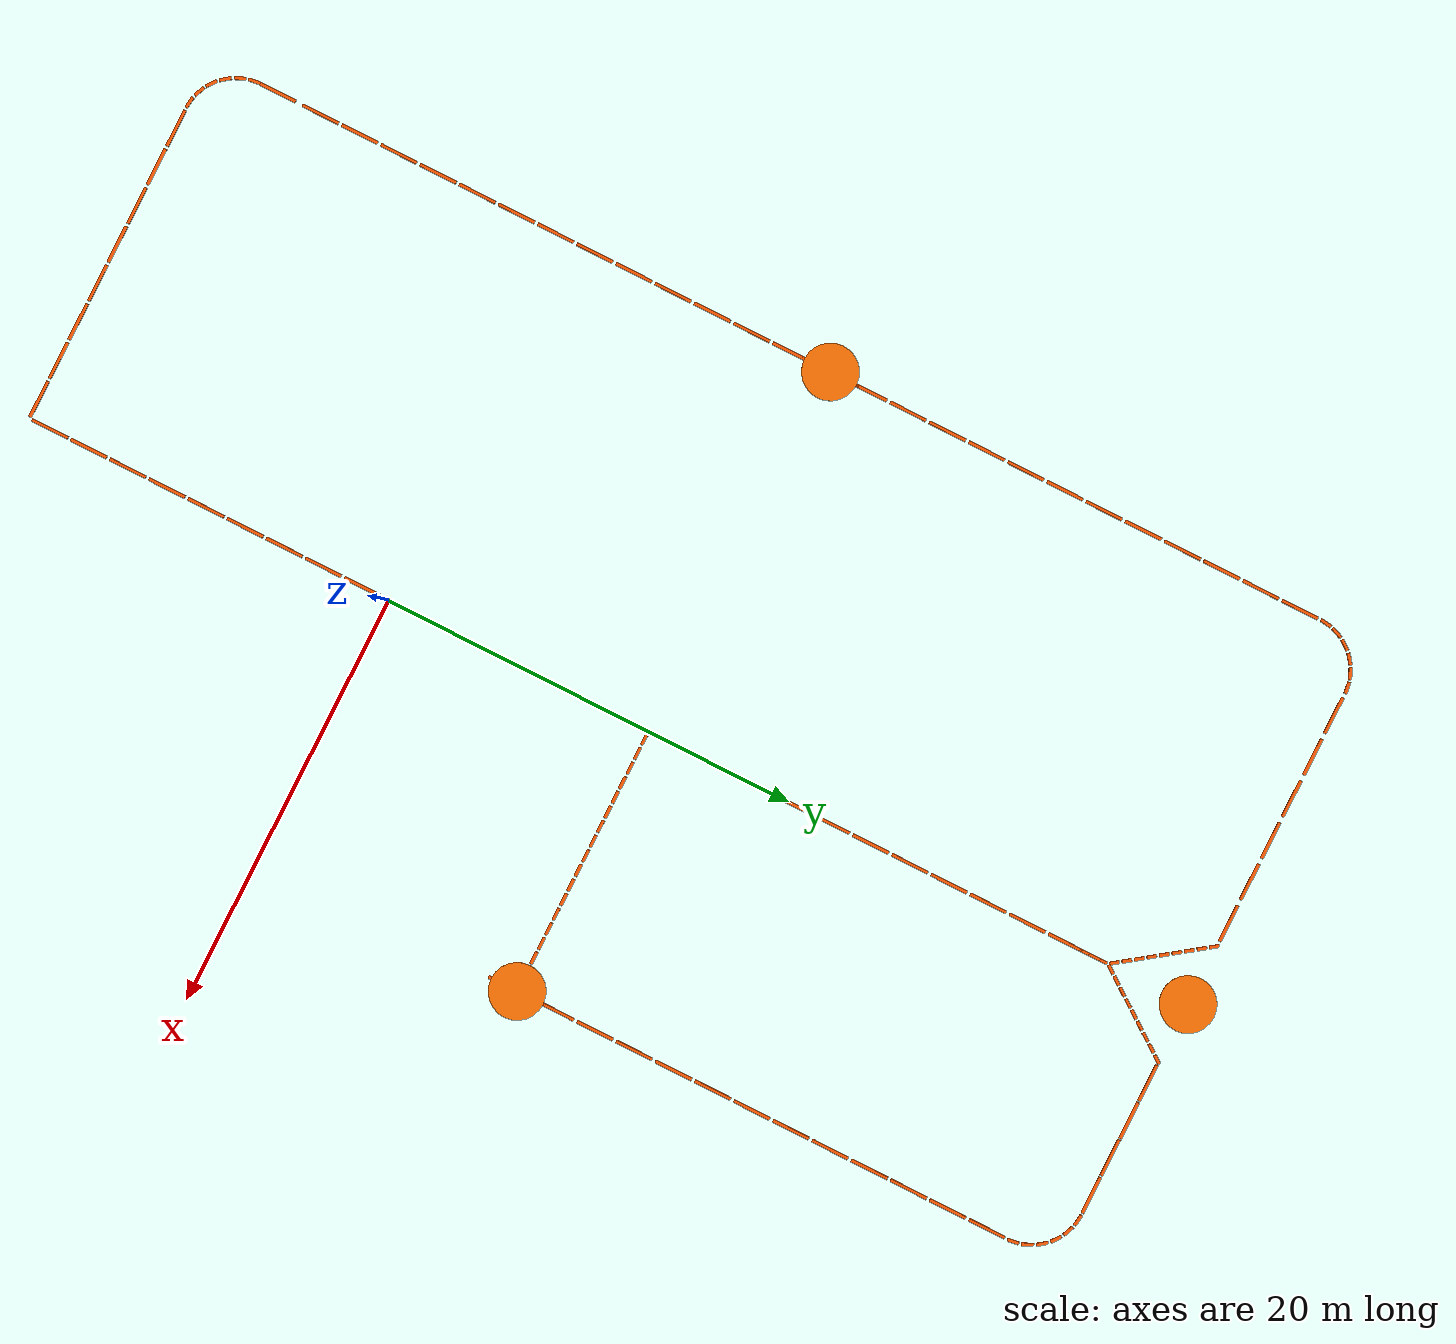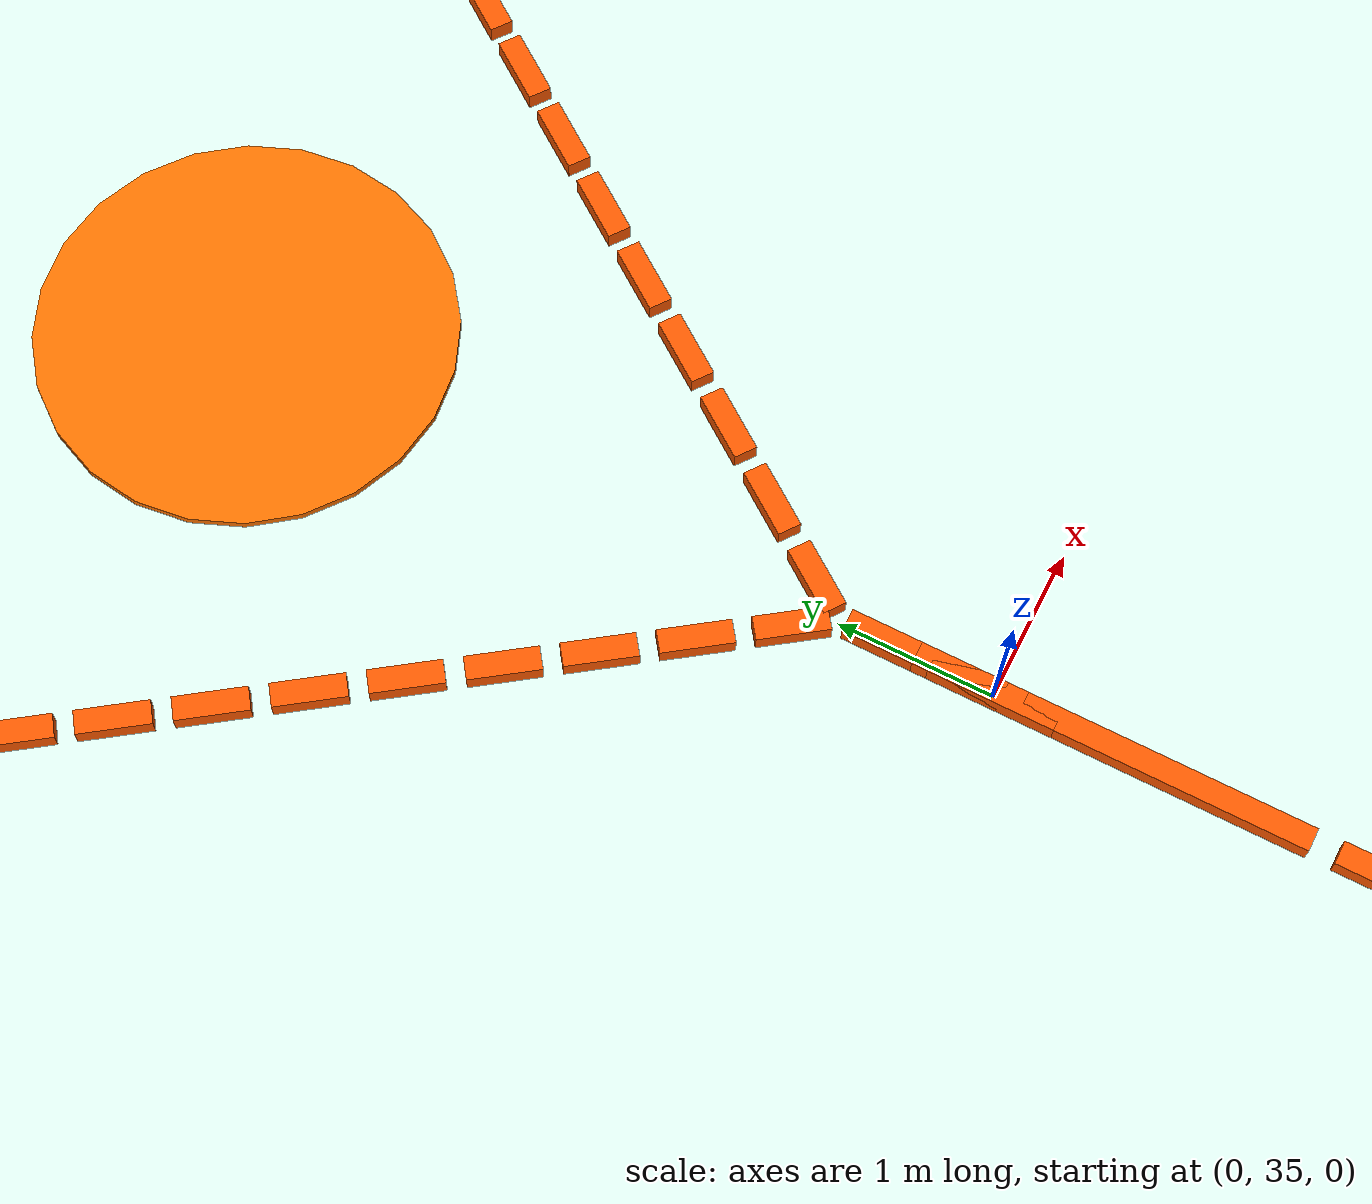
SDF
<sdf version="1.10">
 <world name="warehouse_fuel">
  <gravity>0 0 -9.8000000000000007</gravity>
  <physics name="default_physics" default="false" type="ode">
   <max_step_size>0.01</max_step_size>
   <real_time_factor>1</real_time_factor>
   <real_time_update_rate>100</real_time_update_rate>
   <dart><collision_detector>bullet</collision_detector><solver><solver_type>pgs</solver_type></solver></dart>
  </physics>
  <plugin name="gz::sim::systems::Physics" filename="gz-sim-physics-system"/>
  <plugin name="gz::sim::systems::UserCommands" filename="gz-sim-user-commands-system"/>
  <plugin name="gz::sim::systems::SceneBroadcaster" filename="gz-sim-scene-broadcaster-system"/>
  <plugin name="gz::sim::systems::Sensors" filename="gz-sim-sensors-system">
   <render_engine>ogre2</render_engine>
  </plugin>
  <plugin name="gz::sim::systems::Imu" filename="gz-sim-imu-system"/>
  <plugin name="gz::sim::systems::Contact" filename="gz-sim-contact-system"/>
  <scene>
   <shadows>false</shadows>
   <ambient>0.400000006 0.400000006 0.400000006 1</ambient>
   <background>0.699999988 0.699999988 0.699999988 1</background>
  </scene>
  <magnetic_field>5.5644999999999998e-06 2.2875799999999999e-05 -4.2388400000000002e-05</magnetic_field>
  <atmosphere type="adiabatic"/>
  <model name="hand_signal_spot">
   <static>true</static>
   <pose>0 40 0.1982676088809967 0 0 0</pose>
   <link name="link">
    <visual name="visual">
     <geometry><cylinder><radius>1.3</radius><length>0.050000000000000003</length></cylinder></geometry>
     <material><ambient>1 0.449999988 0 1</ambient><diffuse>1 0.449999988 0 1</diffuse></material>
    </visual>
    <inertial>
     <mass>1</mass>
     <inertia><ixx>1</ixx><ixy>0</ixy><ixz>0</ixz><iyy>1</iyy><iyz>0</iyz><izz>1</izz></inertia>
    </inertial>
   </link>
  </model>
  <light name="sun" type="directional">
   <pose>0 0 10 0 0 0</pose>
   <cast_shadows>false</cast_shadows>
   <intensity>1</intensity>
   <direction>-0.5 0.10000000000000001 -0.90000000000000002</direction>
   <diffuse>0.800000012 0.800000012 0.800000012 1</diffuse>
   <specular>0.200000003 0.200000003 0.200000003 1</specular>
   <attenuation><range>10</range><linear>1</linear><constant>1</constant><quadratic>0</quadratic></attenuation>
   <spot><inner_angle>0</inner_angle><outer_angle>0</outer_angle><falloff>0</falloff></spot>
  </light>
  <model name="track_signal_entry_1">
   <static>true</static>
   <pose>0 35.1 0.06 0 0 -1.5708</pose>
   <link name="link">
    <visual name="visual">
     <geometry><box><size>1 0.15 0.12</size></box></geometry>
     <material>
      <ambient>1 0.349999994 0 1</ambient>
      <diffuse>1 0.349999994 0 1</diffuse>
      <emissive>0.200000003 0.0700000003 0 1</emissive>
     </material>
    </visual>
    <inertial>
     <mass>1</mass>
     <inertia><ixx>1</ixx><ixy>0</ixy><ixz>0</ixz><iyy>1</iyy><iyz>0</iyz><izz>1</izz></inertia>
    </inertial>
   </link>
  </model>
  <model name="track_spine_1">
   <static>true</static>
   <pose>0 33.9212 0.06 0 0 -1.5708</pose>
   <link name="link">
    <visual name="visual">
     <geometry><box><size>1.8 0.15 0.12</size></box></geometry>
     <material>
      <ambient>1 0.349999994 0 1</ambient>
      <diffuse>1 0.349999994 0 1</diffuse>
      <emissive>0.200000003 0.0700000003 0 1</emissive>
     </material>
    </visual>
    <inertial>
     <mass>1</mass>
     <inertia><ixx>1</ixx><ixy>0</ixy><ixz>0</ixz><iyy>1</iyy><iyz>0</iyz><izz>1</izz></inertia>
    </inertial>
   </link>
  </model>
  <model name="track_spine_2">
   <static>true</static>
   <pose>0 31.9635 0.06 0 0 -1.5708</pose>
   <link name="link">
    <visual name="visual">
     <geometry><box><size>1.8 0.15 0.12</size></box></geometry>
     <material>
      <ambient>1 0.349999994 0 1</ambient>
      <diffuse>1 0.349999994 0 1</diffuse>
      <emissive>0.200000003 0.0700000003 0 1</emissive>
     </material>
    </visual>
    <inertial>
     <mass>1</mass>
     <inertia><ixx>1</ixx><ixy>0</ixy><ixz>0</ixz><iyy>1</iyy><iyz>0</iyz><izz>1</izz></inertia>
    </inertial>
   </link>
  </model>
  <model name="track_spine_3">
   <static>true</static>
   <pose>0 30.0058 0.06 0 0 -1.5708</pose>
   <link name="link">
    <visual name="visual">
     <geometry><box><size>1.8 0.15 0.12</size></box></geometry>
     <material>
      <ambient>1 0.349999994 0 1</ambient>
      <diffuse>1 0.349999994 0 1</diffuse>
      <emissive>0.200000003 0.0700000003 0 1</emissive>
     </material>
    </visual>
    <inertial>
     <mass>1</mass>
     <inertia><ixx>1</ixx><ixy>0</ixy><ixz>0</ixz><iyy>1</iyy><iyz>0</iyz><izz>1</izz></inertia>
    </inertial>
   </link>
  </model>
  <model name="track_spine_4">
   <static>true</static>
   <pose>0 28.0481 0.06 0 0 -1.5708</pose>
   <link name="link">
    <visual name="visual">
     <geometry><box><size>1.8 0.15 0.12</size></box></geometry>
     <material>
      <ambient>1 0.349999994 0 1</ambient>
      <diffuse>1 0.349999994 0 1</diffuse>
      <emissive>0.200000003 0.0700000003 0 1</emissive>
     </material>
    </visual>
    <inertial>
     <mass>1</mass>
     <inertia><ixx>1</ixx><ixy>0</ixy><ixz>0</ixz><iyy>1</iyy><iyz>0</iyz><izz>1</izz></inertia>
    </inertial>
   </link>
  </model>
  <model name="track_spine_5">
   <static>true</static>
   <pose>0 26.0904 0.06 0 0 -1.5708</pose>
   <link name="link">
    <visual name="visual">
     <geometry><box><size>1.8 0.15 0.12</size></box></geometry>
     <material>
      <ambient>1 0.349999994 0 1</ambient>
      <diffuse>1 0.349999994 0 1</diffuse>
      <emissive>0.200000003 0.0700000003 0 1</emissive>
     </material>
    </visual>
    <inertial>
     <mass>1</mass>
     <inertia><ixx>1</ixx><ixy>0</ixy><ixz>0</ixz><iyy>1</iyy><iyz>0</iyz><izz>1</izz></inertia>
    </inertial>
   </link>
  </model>
  <model name="track_spine_6">
   <static>true</static>
   <pose>0 24.1327 0.06 0 0 -1.5708</pose>
   <link name="link">
    <visual name="visual">
     <geometry><box><size>1.8 0.15 0.12</size></box></geometry>
     <material>
      <ambient>1 0.349999994 0 1</ambient>
      <diffuse>1 0.349999994 0 1</diffuse>
      <emissive>0.200000003 0.0700000003 0 1</emissive>
     </material>
    </visual>
    <inertial>
     <mass>1</mass>
     <inertia><ixx>1</ixx><ixy>0</ixy><ixz>0</ixz><iyy>1</iyy><iyz>0</iyz><izz>1</izz></inertia>
    </inertial>
   </link>
  </model>
  <model name="track_spine_7">
   <static>true</static>
   <pose>0 22.175 0.06 0 0 -1.5708</pose>
   <link name="link">
    <visual name="visual">
     <geometry><box><size>1.8 0.15 0.12</size></box></geometry>
     <material>
      <ambient>1 0.349999994 0 1</ambient>
      <diffuse>1 0.349999994 0 1</diffuse>
      <emissive>0.200000003 0.0700000003 0 1</emissive>
     </material>
    </visual>
    <inertial>
     <mass>1</mass>
     <inertia><ixx>1</ixx><ixy>0</ixy><ixz>0</ixz><iyy>1</iyy><iyz>0</iyz><izz>1</izz></inertia>
    </inertial>
   </link>
  </model>
  <model name="track_spine_8">
   <static>true</static>
   <pose>0 20.2173 0.06 0 0 -1.5708</pose>
   <link name="link">
    <visual name="visual">
     <geometry><box><size>1.8 0.15 0.12</size></box></geometry>
     <material>
      <ambient>1 0.349999994 0 1</ambient>
      <diffuse>1 0.349999994 0 1</diffuse>
      <emissive>0.200000003 0.0700000003 0 1</emissive>
     </material>
    </visual>
    <inertial>
     <mass>1</mass>
     <inertia><ixx>1</ixx><ixy>0</ixy><ixz>0</ixz><iyy>1</iyy><iyz>0</iyz><izz>1</izz></inertia>
    </inertial>
   </link>
  </model>
  <model name="track_spine_9">
   <static>true</static>
   <pose>0 18.2596 0.06 0 0 -1.5708</pose>
   <link name="link">
    <visual name="visual">
     <geometry><box><size>1.8 0.15 0.12</size></box></geometry>
     <material>
      <ambient>1 0.349999994 0 1</ambient>
      <diffuse>1 0.349999994 0 1</diffuse>
      <emissive>0.200000003 0.0700000003 0 1</emissive>
     </material>
    </visual>
    <inertial>
     <mass>1</mass>
     <inertia><ixx>1</ixx><ixy>0</ixy><ixz>0</ixz><iyy>1</iyy><iyz>0</iyz><izz>1</izz></inertia>
    </inertial>
   </link>
  </model>
  <model name="track_spine_10">
   <static>true</static>
   <pose>0 16.3019 0.06 0 0 -1.5708</pose>
   <link name="link">
    <visual name="visual">
     <geometry><box><size>1.8 0.15 0.12</size></box></geometry>
     <material>
      <ambient>1 0.349999994 0 1</ambient>
      <diffuse>1 0.349999994 0 1</diffuse>
      <emissive>0.200000003 0.0700000003 0 1</emissive>
     </material>
    </visual>
    <inertial>
     <mass>1</mass>
     <inertia><ixx>1</ixx><ixy>0</ixy><ixz>0</ixz><iyy>1</iyy><iyz>0</iyz><izz>1</izz></inertia>
    </inertial>
   </link>
  </model>
  <model name="track_spine_11">
   <static>true</static>
   <pose>0 14.3442 0.06 0 0 -1.5708</pose>
   <link name="link">
    <visual name="visual">
     <geometry><box><size>1.8 0.15 0.12</size></box></geometry>
     <material>
      <ambient>1 0.349999994 0 1</ambient>
      <diffuse>1 0.349999994 0 1</diffuse>
      <emissive>0.200000003 0.0700000003 0 1</emissive>
     </material>
    </visual>
    <inertial>
     <mass>1</mass>
     <inertia><ixx>1</ixx><ixy>0</ixy><ixz>0</ixz><iyy>1</iyy><iyz>0</iyz><izz>1</izz></inertia>
    </inertial>
   </link>
  </model>
  <model name="track_spine_12">
   <static>true</static>
   <pose>0 12.3865 0.06 0 0 -1.5708</pose>
   <link name="link">
    <visual name="visual">
     <geometry><box><size>1.8 0.15 0.12</size></box></geometry>
     <material>
      <ambient>1 0.349999994 0 1</ambient>
      <diffuse>1 0.349999994 0 1</diffuse>
      <emissive>0.200000003 0.0700000003 0 1</emissive>
     </material>
    </visual>
    <inertial>
     <mass>1</mass>
     <inertia><ixx>1</ixx><ixy>0</ixy><ixz>0</ixz><iyy>1</iyy><iyz>0</iyz><izz>1</izz></inertia>
    </inertial>
   </link>
  </model>
  <model name="track_spine_13">
   <static>true</static>
   <pose>0 10.4288 0.06 0 0 -1.5708</pose>
   <link name="link">
    <visual name="visual">
     <geometry><box><size>1.8 0.15 0.12</size></box></geometry>
     <material>
      <ambient>1 0.349999994 0 1</ambient>
      <diffuse>1 0.349999994 0 1</diffuse>
      <emissive>0.200000003 0.0700000003 0 1</emissive>
     </material>
    </visual>
    <inertial>
     <mass>1</mass>
     <inertia><ixx>1</ixx><ixy>0</ixy><ixz>0</ixz><iyy>1</iyy><iyz>0</iyz><izz>1</izz></inertia>
    </inertial>
   </link>
  </model>
  <model name="track_spine_14">
   <static>true</static>
   <pose>0 8.47115 0.06 0 0 -1.5708</pose>
   <link name="link">
    <visual name="visual">
     <geometry><box><size>1.8 0.15 0.12</size></box></geometry>
     <material>
      <ambient>1 0.349999994 0 1</ambient>
      <diffuse>1 0.349999994 0 1</diffuse>
      <emissive>0.200000003 0.0700000003 0 1</emissive>
     </material>
    </visual>
    <inertial>
     <mass>1</mass>
     <inertia><ixx>1</ixx><ixy>0</ixy><ixz>0</ixz><iyy>1</iyy><iyz>0</iyz><izz>1</izz></inertia>
    </inertial>
   </link>
  </model>
  <model name="track_spine_15">
   <static>true</static>
   <pose>0 6.51346 0.06 0 0 -1.5708</pose>
   <link name="link">
    <visual name="visual">
     <geometry><box><size>1.8 0.15 0.12</size></box></geometry>
     <material>
      <ambient>1 0.349999994 0 1</ambient>
      <diffuse>1 0.349999994 0 1</diffuse>
      <emissive>0.200000003 0.0700000003 0 1</emissive>
     </material>
    </visual>
    <inertial>
     <mass>1</mass>
     <inertia><ixx>1</ixx><ixy>0</ixy><ixz>0</ixz><iyy>1</iyy><iyz>0</iyz><izz>1</izz></inertia>
    </inertial>
   </link>
  </model>
  <model name="track_spine_16">
   <static>true</static>
   <pose>0 4.55577 0.06 0 0 -1.5708</pose>
   <link name="link">
    <visual name="visual">
     <geometry><box><size>1.8 0.15 0.12</size></box></geometry>
     <material>
      <ambient>1 0.349999994 0 1</ambient>
      <diffuse>1 0.349999994 0 1</diffuse>
      <emissive>0.200000003 0.0700000003 0 1</emissive>
     </material>
    </visual>
    <inertial>
     <mass>1</mass>
     <inertia><ixx>1</ixx><ixy>0</ixy><ixz>0</ixz><iyy>1</iyy><iyz>0</iyz><izz>1</izz></inertia>
    </inertial>
   </link>
  </model>
  <model name="track_spine_17">
   <static>true</static>
   <pose>0 2.59808 0.06 0 0 -1.5708</pose>
   <link name="link">
    <visual name="visual">
     <geometry><box><size>1.8 0.15 0.12</size></box></geometry>
     <material>
      <ambient>1 0.349999994 0 1</ambient>
      <diffuse>1 0.349999994 0 1</diffuse>
      <emissive>0.200000003 0.0700000003 0 1</emissive>
     </material>
    </visual>
    <inertial>
     <mass>1</mass>
     <inertia><ixx>1</ixx><ixy>0</ixy><ixz>0</ixz><iyy>1</iyy><iyz>0</iyz><izz>1</izz></inertia>
    </inertial>
   </link>
  </model>
  <model name="track_spine_18">
   <static>true</static>
   <pose>0 0.640385 0.06 0 0 -1.5708</pose>
   <link name="link">
    <visual name="visual">
     <geometry><box><size>1.8 0.15 0.12</size></box></geometry>
     <material>
      <ambient>1 0.349999994 0 1</ambient>
      <diffuse>1 0.349999994 0 1</diffuse>
      <emissive>0.200000003 0.0700000003 0 1</emissive>
     </material>
    </visual>
    <inertial>
     <mass>1</mass>
     <inertia><ixx>1</ixx><ixy>0</ixy><ixz>0</ixz><iyy>1</iyy><iyz>0</iyz><izz>1</izz></inertia>
    </inertial>
   </link>
  </model>
  <model name="track_spine_19">
   <static>true</static>
   <pose>0 -1.31731 0.06 0 0 -1.5708</pose>
   <link name="link">
    <visual name="visual">
     <geometry><box><size>1.8 0.15 0.12</size></box></geometry>
     <material>
      <ambient>1 0.349999994 0 1</ambient>
      <diffuse>1 0.349999994 0 1</diffuse>
      <emissive>0.200000003 0.0700000003 0 1</emissive>
     </material>
    </visual>
    <inertial>
     <mass>1</mass>
     <inertia><ixx>1</ixx><ixy>0</ixy><ixz>0</ixz><iyy>1</iyy><iyz>0</iyz><izz>1</izz></inertia>
    </inertial>
   </link>
  </model>
  <model name="track_spine_20">
   <static>true</static>
   <pose>0 -3.275 0.06 0 0 -1.5708</pose>
   <link name="link">
    <visual name="visual">
     <geometry><box><size>1.8 0.15 0.12</size></box></geometry>
     <material>
      <ambient>1 0.349999994 0 1</ambient>
      <diffuse>1 0.349999994 0 1</diffuse>
      <emissive>0.200000003 0.0700000003 0 1</emissive>
     </material>
    </visual>
    <inertial>
     <mass>1</mass>
     <inertia><ixx>1</ixx><ixy>0</ixy><ixz>0</ixz><iyy>1</iyy><iyz>0</iyz><izz>1</izz></inertia>
    </inertial>
   </link>
  </model>
  <model name="track_spine_21">
   <static>true</static>
   <pose>0 -5.23269 0.06 0 0 -1.5708</pose>
   <link name="link">
    <visual name="visual">
     <geometry><box><size>1.8 0.15 0.12</size></box></geometry>
     <material>
      <ambient>1 0.349999994 0 1</ambient>
      <diffuse>1 0.349999994 0 1</diffuse>
      <emissive>0.200000003 0.0700000003 0 1</emissive>
     </material>
    </visual>
    <inertial>
     <mass>1</mass>
     <inertia><ixx>1</ixx><ixy>0</ixy><ixz>0</ixz><iyy>1</iyy><iyz>0</iyz><izz>1</izz></inertia>
    </inertial>
   </link>
  </model>
  <model name="track_spine_22">
   <static>true</static>
   <pose>0 -7.19038 0.06 0 0 -1.5708</pose>
   <link name="link">
    <visual name="visual">
     <geometry><box><size>1.8 0.15 0.12</size></box></geometry>
     <material>
      <ambient>1 0.349999994 0 1</ambient>
      <diffuse>1 0.349999994 0 1</diffuse>
      <emissive>0.200000003 0.0700000003 0 1</emissive>
     </material>
    </visual>
    <inertial>
     <mass>1</mass>
     <inertia><ixx>1</ixx><ixy>0</ixy><ixz>0</ixz><iyy>1</iyy><iyz>0</iyz><izz>1</izz></inertia>
    </inertial>
   </link>
  </model>
  <model name="track_spine_23">
   <static>true</static>
   <pose>0 -9.14808 0.06 0 0 -1.5708</pose>
   <link name="link">
    <visual name="visual">
     <geometry><box><size>1.8 0.15 0.12</size></box></geometry>
     <material>
      <ambient>1 0.349999994 0 1</ambient>
      <diffuse>1 0.349999994 0 1</diffuse>
      <emissive>0.200000003 0.0700000003 0 1</emissive>
     </material>
    </visual>
    <inertial>
     <mass>1</mass>
     <inertia><ixx>1</ixx><ixy>0</ixy><ixz>0</ixz><iyy>1</iyy><iyz>0</iyz><izz>1</izz></inertia>
    </inertial>
   </link>
  </model>
  <model name="track_spine_24">
   <static>true</static>
   <pose>0 -11.1058 0.06 0 0 -1.5708</pose>
   <link name="link">
    <visual name="visual">
     <geometry><box><size>1.8 0.15 0.12</size></box></geometry>
     <material>
      <ambient>1 0.349999994 0 1</ambient>
      <diffuse>1 0.349999994 0 1</diffuse>
      <emissive>0.200000003 0.0700000003 0 1</emissive>
     </material>
    </visual>
    <inertial>
     <mass>1</mass>
     <inertia><ixx>1</ixx><ixy>0</ixy><ixz>0</ixz><iyy>1</iyy><iyz>0</iyz><izz>1</izz></inertia>
    </inertial>
   </link>
  </model>
  <model name="track_spine_25">
   <static>true</static>
   <pose>0 -13.0635 0.06 0 0 -1.5708</pose>
   <link name="link">
    <visual name="visual">
     <geometry><box><size>1.8 0.15 0.12</size></box></geometry>
     <material>
      <ambient>1 0.349999994 0 1</ambient>
      <diffuse>1 0.349999994 0 1</diffuse>
      <emissive>0.200000003 0.0700000003 0 1</emissive>
     </material>
    </visual>
    <inertial>
     <mass>1</mass>
     <inertia><ixx>1</ixx><ixy>0</ixy><ixz>0</ixz><iyy>1</iyy><iyz>0</iyz><izz>1</izz></inertia>
    </inertial>
   </link>
  </model>
  <model name="track_spine_26">
   <static>true</static>
   <pose>0 -15.0212 0.06 0 0 -1.5708</pose>
   <link name="link">
    <visual name="visual">
     <geometry><box><size>1.8 0.15 0.12</size></box></geometry>
     <material>
      <ambient>1 0.349999994 0 1</ambient>
      <diffuse>1 0.349999994 0 1</diffuse>
      <emissive>0.200000003 0.0700000003 0 1</emissive>
     </material>
    </visual>
    <inertial>
     <mass>1</mass>
     <inertia><ixx>1</ixx><ixy>0</ixy><ixz>0</ixz><iyy>1</iyy><iyz>0</iyz><izz>1</izz></inertia>
    </inertial>
   </link>
  </model>
  <model name="track_loop_top_r_1">
   <static>true</static>
   <pose>3.9375 40 0.06 0 0 0</pose>
   <link name="link">
    <visual name="visual">
     <geometry><box><size>1.8 0.15 0.12</size></box></geometry>
     <material>
      <ambient>1 0.349999994 0 1</ambient>
      <diffuse>1 0.349999994 0 1</diffuse>
      <emissive>0.200000003 0.0700000003 0 1</emissive>
     </material>
    </visual>
    <inertial>
     <mass>1</mass>
     <inertia><ixx>1</ixx><ixy>0</ixy><ixz>0</ixz><iyy>1</iyy><iyz>0</iyz><izz>1</izz></inertia>
    </inertial>
   </link>
  </model>
  <model name="track_loop_top_r_2">
   <static>true</static>
   <pose>5.8125 40 0.06 0 0 0</pose>
   <link name="link">
    <visual name="visual">
     <geometry><box><size>1.8 0.15 0.12</size></box></geometry>
     <material>
      <ambient>1 0.349999994 0 1</ambient>
      <diffuse>1 0.349999994 0 1</diffuse>
      <emissive>0.200000003 0.0700000003 0 1</emissive>
     </material>
    </visual>
    <inertial>
     <mass>1</mass>
     <inertia><ixx>1</ixx><ixy>0</ixy><ixz>0</ixz><iyy>1</iyy><iyz>0</iyz><izz>1</izz></inertia>
    </inertial>
   </link>
  </model>
  <model name="track_loop_top_r_3">
   <static>true</static>
   <pose>7.6875 40 0.06 0 0 0</pose>
   <link name="link">
    <visual name="visual">
     <geometry><box><size>1.8 0.15 0.12</size></box></geometry>
     <material>
      <ambient>1 0.349999994 0 1</ambient>
      <diffuse>1 0.349999994 0 1</diffuse>
      <emissive>0.200000003 0.0700000003 0 1</emissive>
     </material>
    </visual>
    <inertial>
     <mass>1</mass>
     <inertia><ixx>1</ixx><ixy>0</ixy><ixz>0</ixz><iyy>1</iyy><iyz>0</iyz><izz>1</izz></inertia>
    </inertial>
   </link>
  </model>
  <model name="track_loop_top_r_4">
   <static>true</static>
   <pose>9.5625 40 0.06 0 0 0</pose>
   <link name="link">
    <visual name="visual">
     <geometry><box><size>1.8 0.15 0.12</size></box></geometry>
     <material>
      <ambient>1 0.349999994 0 1</ambient>
      <diffuse>1 0.349999994 0 1</diffuse>
      <emissive>0.200000003 0.0700000003 0 1</emissive>
     </material>
    </visual>
    <inertial>
     <mass>1</mass>
     <inertia><ixx>1</ixx><ixy>0</ixy><ixz>0</ixz><iyy>1</iyy><iyz>0</iyz><izz>1</izz></inertia>
    </inertial>
   </link>
  </model>
  <model name="track_loop_corner_tr_1">
   <static>true</static>
   <pose>10.8263 39.9786 0.06 0 0 -0.1314</pose>
   <link name="link">
    <visual name="visual">
     <geometry><box><size>0.55 0.15 0.12</size></box></geometry>
     <material>
      <ambient>1 0.349999994 0 1</ambient>
      <diffuse>1 0.349999994 0 1</diffuse>
      <emissive>0.200000003 0.0700000003 0 1</emissive>
     </material>
    </visual>
    <inertial>
     <mass>1</mass>
     <inertia><ixx>1</ixx><ixy>0</ixy><ixz>0</ixz><iyy>1</iyy><iyz>0</iyz><izz>1</izz></inertia>
    </inertial>
   </link>
  </model>
  <model name="track_loop_corner_tr_2">
   <static>true</static>
   <pose>11.4567 39.8097 0.06 0 0 -0.393199</pose>
   <link name="link">
    <visual name="visual">
     <geometry><box><size>0.55 0.15 0.12</size></box></geometry>
     <material>
      <ambient>1 0.349999994 0 1</ambient>
      <diffuse>1 0.349999994 0 1</diffuse>
      <emissive>0.200000003 0.0700000003 0 1</emissive>
     </material>
    </visual>
    <inertial>
     <mass>1</mass>
     <inertia><ixx>1</ixx><ixy>0</ixy><ixz>0</ixz><iyy>1</iyy><iyz>0</iyz><izz>1</izz></inertia>
    </inertial>
   </link>
  </model>
  <model name="track_loop_corner_tr_3">
   <static>true</static>
   <pose>12.0219 39.4834 0.06 0 0 -0.654998</pose>
   <link name="link">
    <visual name="visual">
     <geometry><box><size>0.55 0.15 0.12</size></box></geometry>
     <material>
      <ambient>1 0.349999994 0 1</ambient>
      <diffuse>1 0.349999994 0 1</diffuse>
      <emissive>0.200000003 0.0700000003 0 1</emissive>
     </material>
    </visual>
    <inertial>
     <mass>1</mass>
     <inertia><ixx>1</ixx><ixy>0</ixy><ixz>0</ixz><iyy>1</iyy><iyz>0</iyz><izz>1</izz></inertia>
    </inertial>
   </link>
  </model>
  <model name="track_loop_corner_tr_4">
   <static>true</static>
   <pose>12.4834 39.0219 0.06 0 0 -0.916798</pose>
   <link name="link">
    <visual name="visual">
     <geometry><box><size>0.55 0.15 0.12</size></box></geometry>
     <material>
      <ambient>1 0.349999994 0 1</ambient>
      <diffuse>1 0.349999994 0 1</diffuse>
      <emissive>0.200000003 0.0700000003 0 1</emissive>
     </material>
    </visual>
    <inertial>
     <mass>1</mass>
     <inertia><ixx>1</ixx><ixy>0</ixy><ixz>0</ixz><iyy>1</iyy><iyz>0</iyz><izz>1</izz></inertia>
    </inertial>
   </link>
  </model>
  <model name="track_loop_corner_tr_5">
   <static>true</static>
   <pose>12.8097 38.4567 0.06 0 0 -1.1786</pose>
   <link name="link">
    <visual name="visual">
     <geometry><box><size>0.55 0.15 0.12</size></box></geometry>
     <material>
      <ambient>1 0.349999994 0 1</ambient>
      <diffuse>1 0.349999994 0 1</diffuse>
      <emissive>0.200000003 0.0700000003 0 1</emissive>
     </material>
    </visual>
    <inertial>
     <mass>1</mass>
     <inertia><ixx>1</ixx><ixy>0</ixy><ixz>0</ixz><iyy>1</iyy><iyz>0</iyz><izz>1</izz></inertia>
    </inertial>
   </link>
  </model>
  <model name="track_loop_corner_tr_6">
   <static>true</static>
   <pose>12.9786 37.8263 0.06 0 0 -1.4404</pose>
   <link name="link">
    <visual name="visual">
     <geometry><box><size>0.55 0.15 0.12</size></box></geometry>
     <material>
      <ambient>1 0.349999994 0 1</ambient>
      <diffuse>1 0.349999994 0 1</diffuse>
      <emissive>0.200000003 0.0700000003 0 1</emissive>
     </material>
    </visual>
    <inertial>
     <mass>1</mass>
     <inertia><ixx>1</ixx><ixy>0</ixy><ixz>0</ixz><iyy>1</iyy><iyz>0</iyz><izz>1</izz></inertia>
    </inertial>
   </link>
  </model>
  <model name="track_loop_right_1">
   <static>true</static>
   <pose>13 36.5192 0.06 0 0 -1.5708</pose>
   <link name="link">
    <visual name="visual">
     <geometry><box><size>1.8 0.15 0.12</size></box></geometry>
     <material>
      <ambient>1 0.349999994 0 1</ambient>
      <diffuse>1 0.349999994 0 1</diffuse>
      <emissive>0.200000003 0.0700000003 0 1</emissive>
     </material>
    </visual>
    <inertial>
     <mass>1</mass>
     <inertia><ixx>1</ixx><ixy>0</ixy><ixz>0</ixz><iyy>1</iyy><iyz>0</iyz><izz>1</izz></inertia>
    </inertial>
   </link>
  </model>
  <model name="track_loop_right_2">
   <static>true</static>
   <pose>13 34.5577 0.06 0 0 -1.5708</pose>
   <link name="link">
    <visual name="visual">
     <geometry><box><size>1.8 0.15 0.12</size></box></geometry>
     <material>
      <ambient>1 0.349999994 0 1</ambient>
      <diffuse>1 0.349999994 0 1</diffuse>
      <emissive>0.200000003 0.0700000003 0 1</emissive>
     </material>
    </visual>
    <inertial>
     <mass>1</mass>
     <inertia><ixx>1</ixx><ixy>0</ixy><ixz>0</ixz><iyy>1</iyy><iyz>0</iyz><izz>1</izz></inertia>
    </inertial>
   </link>
  </model>
  <model name="track_loop_right_3">
   <static>true</static>
   <pose>13 32.5962 0.06 0 0 -1.5708</pose>
   <link name="link">
    <visual name="visual">
     <geometry><box><size>1.8 0.15 0.12</size></box></geometry>
     <material>
      <ambient>1 0.349999994 0 1</ambient>
      <diffuse>1 0.349999994 0 1</diffuse>
      <emissive>0.200000003 0.0700000003 0 1</emissive>
     </material>
    </visual>
    <inertial>
     <mass>1</mass>
     <inertia><ixx>1</ixx><ixy>0</ixy><ixz>0</ixz><iyy>1</iyy><iyz>0</iyz><izz>1</izz></inertia>
    </inertial>
   </link>
  </model>
  <model name="track_loop_right_4">
   <static>true</static>
   <pose>13 30.6346 0.06 0 0 -1.5708</pose>
   <link name="link">
    <visual name="visual">
     <geometry><box><size>1.8 0.15 0.12</size></box></geometry>
     <material>
      <ambient>1 0.349999994 0 1</ambient>
      <diffuse>1 0.349999994 0 1</diffuse>
      <emissive>0.200000003 0.0700000003 0 1</emissive>
     </material>
    </visual>
    <inertial>
     <mass>1</mass>
     <inertia><ixx>1</ixx><ixy>0</ixy><ixz>0</ixz><iyy>1</iyy><iyz>0</iyz><izz>1</izz></inertia>
    </inertial>
   </link>
  </model>
  <model name="track_loop_right_5">
   <static>true</static>
   <pose>13 28.6731 0.06 0 0 -1.5708</pose>
   <link name="link">
    <visual name="visual">
     <geometry><box><size>1.8 0.15 0.12</size></box></geometry>
     <material>
      <ambient>1 0.349999994 0 1</ambient>
      <diffuse>1 0.349999994 0 1</diffuse>
      <emissive>0.200000003 0.0700000003 0 1</emissive>
     </material>
    </visual>
    <inertial>
     <mass>1</mass>
     <inertia><ixx>1</ixx><ixy>0</ixy><ixz>0</ixz><iyy>1</iyy><iyz>0</iyz><izz>1</izz></inertia>
    </inertial>
   </link>
  </model>
  <model name="track_loop_right_6">
   <static>true</static>
   <pose>13 26.7115 0.06 0 0 -1.5708</pose>
   <link name="link">
    <visual name="visual">
     <geometry><box><size>1.8 0.15 0.12</size></box></geometry>
     <material>
      <ambient>1 0.349999994 0 1</ambient>
      <diffuse>1 0.349999994 0 1</diffuse>
      <emissive>0.200000003 0.0700000003 0 1</emissive>
     </material>
    </visual>
    <inertial>
     <mass>1</mass>
     <inertia><ixx>1</ixx><ixy>0</ixy><ixz>0</ixz><iyy>1</iyy><iyz>0</iyz><izz>1</izz></inertia>
    </inertial>
   </link>
  </model>
  <model name="track_loop_right_7">
   <static>true</static>
   <pose>13 24.75 0.06 0 0 -1.5708</pose>
   <link name="link">
    <visual name="visual">
     <geometry><box><size>1.8 0.15 0.12</size></box></geometry>
     <material>
      <ambient>1 0.349999994 0 1</ambient>
      <diffuse>1 0.349999994 0 1</diffuse>
      <emissive>0.200000003 0.0700000003 0 1</emissive>
     </material>
    </visual>
    <inertial>
     <mass>1</mass>
     <inertia><ixx>1</ixx><ixy>0</ixy><ixz>0</ixz><iyy>1</iyy><iyz>0</iyz><izz>1</izz></inertia>
    </inertial>
   </link>
  </model>
  <model name="track_loop_right_8">
   <static>true</static>
   <pose>13 22.7885 0.06 0 0 -1.5708</pose>
   <link name="link">
    <visual name="visual">
     <geometry><box><size>1.8 0.15 0.12</size></box></geometry>
     <material>
      <ambient>1 0.349999994 0 1</ambient>
      <diffuse>1 0.349999994 0 1</diffuse>
      <emissive>0.200000003 0.0700000003 0 1</emissive>
     </material>
    </visual>
    <inertial>
     <mass>1</mass>
     <inertia><ixx>1</ixx><ixy>0</ixy><ixz>0</ixz><iyy>1</iyy><iyz>0</iyz><izz>1</izz></inertia>
    </inertial>
   </link>
  </model>
  <model name="track_loop_right_9">
   <static>true</static>
   <pose>13 20.8269 0.06 0 0 -1.5708</pose>
   <link name="link">
    <visual name="visual">
     <geometry><box><size>1.8 0.15 0.12</size></box></geometry>
     <material>
      <ambient>1 0.349999994 0 1</ambient>
      <diffuse>1 0.349999994 0 1</diffuse>
      <emissive>0.200000003 0.0700000003 0 1</emissive>
     </material>
    </visual>
    <inertial>
     <mass>1</mass>
     <inertia><ixx>1</ixx><ixy>0</ixy><ixz>0</ixz><iyy>1</iyy><iyz>0</iyz><izz>1</izz></inertia>
    </inertial>
   </link>
  </model>
  <model name="track_loop_right_10">
   <static>true</static>
   <pose>13 18.8654 0.06 0 0 -1.5708</pose>
   <link name="link">
    <visual name="visual">
     <geometry><box><size>1.8 0.15 0.12</size></box></geometry>
     <material>
      <ambient>1 0.349999994 0 1</ambient>
      <diffuse>1 0.349999994 0 1</diffuse>
      <emissive>0.200000003 0.0700000003 0 1</emissive>
     </material>
    </visual>
    <inertial>
     <mass>1</mass>
     <inertia><ixx>1</ixx><ixy>0</ixy><ixz>0</ixz><iyy>1</iyy><iyz>0</iyz><izz>1</izz></inertia>
    </inertial>
   </link>
  </model>
  <model name="track_loop_right_11">
   <static>true</static>
   <pose>13 16.9038 0.06 0 0 -1.5708</pose>
   <link name="link">
    <visual name="visual">
     <geometry><box><size>1.8 0.15 0.12</size></box></geometry>
     <material>
      <ambient>1 0.349999994 0 1</ambient>
      <diffuse>1 0.349999994 0 1</diffuse>
      <emissive>0.200000003 0.0700000003 0 1</emissive>
     </material>
    </visual>
    <inertial>
     <mass>1</mass>
     <inertia><ixx>1</ixx><ixy>0</ixy><ixz>0</ixz><iyy>1</iyy><iyz>0</iyz><izz>1</izz></inertia>
    </inertial>
   </link>
  </model>
  <model name="track_loop_right_12">
   <static>true</static>
   <pose>13 14.9423 0.06 0 0 -1.5708</pose>
   <link name="link">
    <visual name="visual">
     <geometry><box><size>1.8 0.15 0.12</size></box></geometry>
     <material>
      <ambient>1 0.349999994 0 1</ambient>
      <diffuse>1 0.349999994 0 1</diffuse>
      <emissive>0.200000003 0.0700000003 0 1</emissive>
     </material>
    </visual>
    <inertial>
     <mass>1</mass>
     <inertia><ixx>1</ixx><ixy>0</ixy><ixz>0</ixz><iyy>1</iyy><iyz>0</iyz><izz>1</izz></inertia>
    </inertial>
   </link>
  </model>
  <model name="track_loop_top_l_1">
   <static>true</static>
   <pose>-14.4583 40 0.06 0 0 0</pose>
   <link name="link">
    <visual name="visual">
     <geometry><box><size>1.8 0.15 0.12</size></box></geometry>
     <material>
      <ambient>1 0.349999994 0 1</ambient>
      <diffuse>1 0.349999994 0 1</diffuse>
      <emissive>0.200000003 0.0700000003 0 1</emissive>
     </material>
    </visual>
    <inertial>
     <mass>1</mass>
     <inertia><ixx>1</ixx><ixy>0</ixy><ixz>0</ixz><iyy>1</iyy><iyz>0</iyz><izz>1</izz></inertia>
    </inertial>
   </link>
  </model>
  <model name="track_loop_top_l_2">
   <static>true</static>
   <pose>-12.375 40 0.06 0 0 0</pose>
   <link name="link">
    <visual name="visual">
     <geometry><box><size>1.8 0.15 0.12</size></box></geometry>
     <material>
      <ambient>1 0.349999994 0 1</ambient>
      <diffuse>1 0.349999994 0 1</diffuse>
      <emissive>0.200000003 0.0700000003 0 1</emissive>
     </material>
    </visual>
    <inertial>
     <mass>1</mass>
     <inertia><ixx>1</ixx><ixy>0</ixy><ixz>0</ixz><iyy>1</iyy><iyz>0</iyz><izz>1</izz></inertia>
    </inertial>
   </link>
  </model>
  <model name="track_loop_top_l_3">
   <static>true</static>
   <pose>-10.2917 40 0.06 0 0 0</pose>
   <link name="link">
    <visual name="visual">
     <geometry><box><size>1.8 0.15 0.12</size></box></geometry>
     <material>
      <ambient>1 0.349999994 0 1</ambient>
      <diffuse>1 0.349999994 0 1</diffuse>
      <emissive>0.200000003 0.0700000003 0 1</emissive>
     </material>
    </visual>
    <inertial>
     <mass>1</mass>
     <inertia><ixx>1</ixx><ixy>0</ixy><ixz>0</ixz><iyy>1</iyy><iyz>0</iyz><izz>1</izz></inertia>
    </inertial>
   </link>
  </model>
  <model name="track_loop_top_l_4">
   <static>true</static>
   <pose>-8.20833 40 0.06 0 0 0</pose>
   <link name="link">
    <visual name="visual">
     <geometry><box><size>1.8 0.15 0.12</size></box></geometry>
     <material>
      <ambient>1 0.349999994 0 1</ambient>
      <diffuse>1 0.349999994 0 1</diffuse>
      <emissive>0.200000003 0.0700000003 0 1</emissive>
     </material>
    </visual>
    <inertial>
     <mass>1</mass>
     <inertia><ixx>1</ixx><ixy>0</ixy><ixz>0</ixz><iyy>1</iyy><iyz>0</iyz><izz>1</izz></inertia>
    </inertial>
   </link>
  </model>
  <model name="track_loop_top_l_5">
   <static>true</static>
   <pose>-6.125 40 0.06 0 0 0</pose>
   <link name="link">
    <visual name="visual">
     <geometry><box><size>1.8 0.15 0.12</size></box></geometry>
     <material>
      <ambient>1 0.349999994 0 1</ambient>
      <diffuse>1 0.349999994 0 1</diffuse>
      <emissive>0.200000003 0.0700000003 0 1</emissive>
     </material>
    </visual>
    <inertial>
     <mass>1</mass>
     <inertia><ixx>1</ixx><ixy>0</ixy><ixz>0</ixz><iyy>1</iyy><iyz>0</iyz><izz>1</izz></inertia>
    </inertial>
   </link>
  </model>
  <model name="track_loop_top_l_6">
   <static>true</static>
   <pose>-4.04167 40 0.06 0 0 0</pose>
   <link name="link">
    <visual name="visual">
     <geometry><box><size>1.8 0.15 0.12</size></box></geometry>
     <material>
      <ambient>1 0.349999994 0 1</ambient>
      <diffuse>1 0.349999994 0 1</diffuse>
      <emissive>0.200000003 0.0700000003 0 1</emissive>
     </material>
    </visual>
    <inertial>
     <mass>1</mass>
     <inertia><ixx>1</ixx><ixy>0</ixy><ixz>0</ixz><iyy>1</iyy><iyz>0</iyz><izz>1</izz></inertia>
    </inertial>
   </link>
  </model>
  <model name="track_loop_corner_tl_1">
   <static>true</static>
   <pose>-17.9786 37.8263 0.06 0 0 1.4394</pose>
   <link name="link">
    <visual name="visual">
     <geometry><box><size>0.55 0.15 0.12</size></box></geometry>
     <material>
      <ambient>1 0.349999994 0 1</ambient>
      <diffuse>1 0.349999994 0 1</diffuse>
      <emissive>0.200000003 0.0700000003 0 1</emissive>
     </material>
    </visual>
    <inertial>
     <mass>1</mass>
     <inertia><ixx>1</ixx><ixy>0</ixy><ixz>0</ixz><iyy>1</iyy><iyz>0</iyz><izz>1</izz></inertia>
    </inertial>
   </link>
  </model>
  <model name="track_loop_corner_tl_2">
   <static>true</static>
   <pose>-17.8097 38.4567 0.06 0 0 1.1776</pose>
   <link name="link">
    <visual name="visual">
     <geometry><box><size>0.55 0.15 0.12</size></box></geometry>
     <material>
      <ambient>1 0.349999994 0 1</ambient>
      <diffuse>1 0.349999994 0 1</diffuse>
      <emissive>0.200000003 0.0700000003 0 1</emissive>
     </material>
    </visual>
    <inertial>
     <mass>1</mass>
     <inertia><ixx>1</ixx><ixy>0</ixy><ixz>0</ixz><iyy>1</iyy><iyz>0</iyz><izz>1</izz></inertia>
    </inertial>
   </link>
  </model>
  <model name="track_loop_corner_tl_3">
   <static>true</static>
   <pose>-17.4834 39.0219 0.06 0 0 0.915798</pose>
   <link name="link">
    <visual name="visual">
     <geometry><box><size>0.55 0.15 0.12</size></box></geometry>
     <material>
      <ambient>1 0.349999994 0 1</ambient>
      <diffuse>1 0.349999994 0 1</diffuse>
      <emissive>0.200000003 0.0700000003 0 1</emissive>
     </material>
    </visual>
    <inertial>
     <mass>1</mass>
     <inertia><ixx>1</ixx><ixy>0</ixy><ixz>0</ixz><iyy>1</iyy><iyz>0</iyz><izz>1</izz></inertia>
    </inertial>
   </link>
  </model>
  <model name="track_loop_corner_tl_4">
   <static>true</static>
   <pose>-17.0219 39.4834 0.06 0 0 0.653998</pose>
   <link name="link">
    <visual name="visual">
     <geometry><box><size>0.55 0.15 0.12</size></box></geometry>
     <material>
      <ambient>1 0.349999994 0 1</ambient>
      <diffuse>1 0.349999994 0 1</diffuse>
      <emissive>0.200000003 0.0700000003 0 1</emissive>
     </material>
    </visual>
    <inertial>
     <mass>1</mass>
     <inertia><ixx>1</ixx><ixy>0</ixy><ixz>0</ixz><iyy>1</iyy><iyz>0</iyz><izz>1</izz></inertia>
    </inertial>
   </link>
  </model>
  <model name="track_loop_corner_tl_5">
   <static>true</static>
   <pose>-16.4567 39.8097 0.06 0 0 0.392199</pose>
   <link name="link">
    <visual name="visual">
     <geometry><box><size>0.55 0.15 0.12</size></box></geometry>
     <material>
      <ambient>1 0.349999994 0 1</ambient>
      <diffuse>1 0.349999994 0 1</diffuse>
      <emissive>0.200000003 0.0700000003 0 1</emissive>
     </material>
    </visual>
    <inertial>
     <mass>1</mass>
     <inertia><ixx>1</ixx><ixy>0</ixy><ixz>0</ixz><iyy>1</iyy><iyz>0</iyz><izz>1</izz></inertia>
    </inertial>
   </link>
  </model>
  <model name="track_loop_corner_tl_6">
   <static>true</static>
   <pose>-15.8263 39.9786 0.06 0 0 0.1304</pose>
   <link name="link">
    <visual name="visual">
     <geometry><box><size>0.55 0.15 0.12</size></box></geometry>
     <material>
      <ambient>1 0.349999994 0 1</ambient>
      <diffuse>1 0.349999994 0 1</diffuse>
      <emissive>0.200000003 0.0700000003 0 1</emissive>
     </material>
    </visual>
    <inertial>
     <mass>1</mass>
     <inertia><ixx>1</ixx><ixy>0</ixy><ixz>0</ixz><iyy>1</iyy><iyz>0</iyz><izz>1</izz></inertia>
    </inertial>
   </link>
  </model>
  <model name="track_loop_left_1">
   <static>true</static>
   <pose>-18 -12.5192 0.06 0 0 1.5708</pose>
   <link name="link">
    <visual name="visual">
     <geometry><box><size>1.8 0.15 0.12</size></box></geometry>
     <material>
      <ambient>1 0.349999994 0 1</ambient>
      <diffuse>1 0.349999994 0 1</diffuse>
      <emissive>0.200000003 0.0700000003 0 1</emissive>
     </material>
    </visual>
    <inertial>
     <mass>1</mass>
     <inertia><ixx>1</ixx><ixy>0</ixy><ixz>0</ixz><iyy>1</iyy><iyz>0</iyz><izz>1</izz></inertia>
    </inertial>
   </link>
  </model>
  <model name="track_loop_left_2">
   <static>true</static>
   <pose>-18 -10.5577 0.06 0 0 1.5708</pose>
   <link name="link">
    <visual name="visual">
     <geometry><box><size>1.8 0.15 0.12</size></box></geometry>
     <material>
      <ambient>1 0.349999994 0 1</ambient>
      <diffuse>1 0.349999994 0 1</diffuse>
      <emissive>0.200000003 0.0700000003 0 1</emissive>
     </material>
    </visual>
    <inertial>
     <mass>1</mass>
     <inertia><ixx>1</ixx><ixy>0</ixy><ixz>0</ixz><iyy>1</iyy><iyz>0</iyz><izz>1</izz></inertia>
    </inertial>
   </link>
  </model>
  <model name="track_loop_left_3">
   <static>true</static>
   <pose>-18 -8.59615 0.06 0 0 1.5708</pose>
   <link name="link">
    <visual name="visual">
     <geometry><box><size>1.8 0.15 0.12</size></box></geometry>
     <material>
      <ambient>1 0.349999994 0 1</ambient>
      <diffuse>1 0.349999994 0 1</diffuse>
      <emissive>0.200000003 0.0700000003 0 1</emissive>
     </material>
    </visual>
    <inertial>
     <mass>1</mass>
     <inertia><ixx>1</ixx><ixy>0</ixy><ixz>0</ixz><iyy>1</iyy><iyz>0</iyz><izz>1</izz></inertia>
    </inertial>
   </link>
  </model>
  <model name="track_loop_left_4">
   <static>true</static>
   <pose>-18 -6.63462 0.06 0 0 1.5708</pose>
   <link name="link">
    <visual name="visual">
     <geometry><box><size>1.8 0.15 0.12</size></box></geometry>
     <material>
      <ambient>1 0.349999994 0 1</ambient>
      <diffuse>1 0.349999994 0 1</diffuse>
      <emissive>0.200000003 0.0700000003 0 1</emissive>
     </material>
    </visual>
    <inertial>
     <mass>1</mass>
     <inertia><ixx>1</ixx><ixy>0</ixy><ixz>0</ixz><iyy>1</iyy><iyz>0</iyz><izz>1</izz></inertia>
    </inertial>
   </link>
  </model>
  <model name="track_loop_left_5">
   <static>true</static>
   <pose>-18 -4.67308 0.06 0 0 1.5708</pose>
   <link name="link">
    <visual name="visual">
     <geometry><box><size>1.8 0.15 0.12</size></box></geometry>
     <material>
      <ambient>1 0.349999994 0 1</ambient>
      <diffuse>1 0.349999994 0 1</diffuse>
      <emissive>0.200000003 0.0700000003 0 1</emissive>
     </material>
    </visual>
    <inertial>
     <mass>1</mass>
     <inertia><ixx>1</ixx><ixy>0</ixy><ixz>0</ixz><iyy>1</iyy><iyz>0</iyz><izz>1</izz></inertia>
    </inertial>
   </link>
  </model>
  <model name="track_loop_left_6">
   <static>true</static>
   <pose>-18 -2.71154 0.06 0 0 1.5708</pose>
   <link name="link">
    <visual name="visual">
     <geometry><box><size>1.8 0.15 0.12</size></box></geometry>
     <material>
      <ambient>1 0.349999994 0 1</ambient>
      <diffuse>1 0.349999994 0 1</diffuse>
      <emissive>0.200000003 0.0700000003 0 1</emissive>
     </material>
    </visual>
    <inertial>
     <mass>1</mass>
     <inertia><ixx>1</ixx><ixy>0</ixy><ixz>0</ixz><iyy>1</iyy><iyz>0</iyz><izz>1</izz></inertia>
    </inertial>
   </link>
  </model>
  <model name="track_loop_left_7">
   <static>true</static>
   <pose>-18 -0.75 0.06 0 0 1.5708</pose>
   <link name="link">
    <visual name="visual">
     <geometry><box><size>1.8 0.15 0.12</size></box></geometry>
     <material>
      <ambient>1 0.349999994 0 1</ambient>
      <diffuse>1 0.349999994 0 1</diffuse>
      <emissive>0.200000003 0.0700000003 0 1</emissive>
     </material>
    </visual>
    <inertial>
     <mass>1</mass>
     <inertia><ixx>1</ixx><ixy>0</ixy><ixz>0</ixz><iyy>1</iyy><iyz>0</iyz><izz>1</izz></inertia>
    </inertial>
   </link>
  </model>
  <model name="track_loop_left_8">
   <static>true</static>
   <pose>-18 1.21154 0.06 0 0 1.5708</pose>
   <link name="link">
    <visual name="visual">
     <geometry><box><size>1.8 0.15 0.12</size></box></geometry>
     <material>
      <ambient>1 0.349999994 0 1</ambient>
      <diffuse>1 0.349999994 0 1</diffuse>
      <emissive>0.200000003 0.0700000003 0 1</emissive>
     </material>
    </visual>
    <inertial>
     <mass>1</mass>
     <inertia><ixx>1</ixx><ixy>0</ixy><ixz>0</ixz><iyy>1</iyy><iyz>0</iyz><izz>1</izz></inertia>
    </inertial>
   </link>
  </model>
  <model name="track_loop_left_9">
   <static>true</static>
   <pose>-18 3.17308 0.06 0 0 1.5708</pose>
   <link name="link">
    <visual name="visual">
     <geometry><box><size>1.8 0.15 0.12</size></box></geometry>
     <material>
      <ambient>1 0.349999994 0 1</ambient>
      <diffuse>1 0.349999994 0 1</diffuse>
      <emissive>0.200000003 0.0700000003 0 1</emissive>
     </material>
    </visual>
    <inertial>
     <mass>1</mass>
     <inertia><ixx>1</ixx><ixy>0</ixy><ixz>0</ixz><iyy>1</iyy><iyz>0</iyz><izz>1</izz></inertia>
    </inertial>
   </link>
  </model>
  <model name="track_loop_left_10">
   <static>true</static>
   <pose>-18 5.13462 0.06 0 0 1.5708</pose>
   <link name="link">
    <visual name="visual">
     <geometry><box><size>1.8 0.15 0.12</size></box></geometry>
     <material>
      <ambient>1 0.349999994 0 1</ambient>
      <diffuse>1 0.349999994 0 1</diffuse>
      <emissive>0.200000003 0.0700000003 0 1</emissive>
     </material>
    </visual>
    <inertial>
     <mass>1</mass>
     <inertia><ixx>1</ixx><ixy>0</ixy><ixz>0</ixz><iyy>1</iyy><iyz>0</iyz><izz>1</izz></inertia>
    </inertial>
   </link>
  </model>
  <model name="track_loop_left_11">
   <static>true</static>
   <pose>-18 7.09615 0.06 0 0 1.5708</pose>
   <link name="link">
    <visual name="visual">
     <geometry><box><size>1.8 0.15 0.12</size></box></geometry>
     <material>
      <ambient>1 0.349999994 0 1</ambient>
      <diffuse>1 0.349999994 0 1</diffuse>
      <emissive>0.200000003 0.0700000003 0 1</emissive>
     </material>
    </visual>
    <inertial>
     <mass>1</mass>
     <inertia><ixx>1</ixx><ixy>0</ixy><ixz>0</ixz><iyy>1</iyy><iyz>0</iyz><izz>1</izz></inertia>
    </inertial>
   </link>
  </model>
  <model name="track_loop_left_12">
   <static>true</static>
   <pose>-18 9.05769 0.06 0 0 1.5708</pose>
   <link name="link">
    <visual name="visual">
     <geometry><box><size>1.8 0.15 0.12</size></box></geometry>
     <material>
      <ambient>1 0.349999994 0 1</ambient>
      <diffuse>1 0.349999994 0 1</diffuse>
      <emissive>0.200000003 0.0700000003 0 1</emissive>
     </material>
    </visual>
    <inertial>
     <mass>1</mass>
     <inertia><ixx>1</ixx><ixy>0</ixy><ixz>0</ixz><iyy>1</iyy><iyz>0</iyz><izz>1</izz></inertia>
    </inertial>
   </link>
  </model>
  <model name="track_loop_left_13">
   <static>true</static>
   <pose>-18 11.0192 0.06 0 0 1.5708</pose>
   <link name="link">
    <visual name="visual">
     <geometry><box><size>1.8 0.15 0.12</size></box></geometry>
     <material>
      <ambient>1 0.349999994 0 1</ambient>
      <diffuse>1 0.349999994 0 1</diffuse>
      <emissive>0.200000003 0.0700000003 0 1</emissive>
     </material>
    </visual>
    <inertial>
     <mass>1</mass>
     <inertia><ixx>1</ixx><ixy>0</ixy><ixz>0</ixz><iyy>1</iyy><iyz>0</iyz><izz>1</izz></inertia>
    </inertial>
   </link>
  </model>
  <model name="track_loop_left_15">
   <static>true</static>
   <pose>-18 14.9423 0.06 0 0 1.5708</pose>
   <link name="link">
    <visual name="visual">
     <geometry><box><size>1.8 0.15 0.12</size></box></geometry>
     <material>
      <ambient>1 0.349999994 0 1</ambient>
      <diffuse>1 0.349999994 0 1</diffuse>
      <emissive>0.200000003 0.0700000003 0 1</emissive>
     </material>
    </visual>
    <inertial>
     <mass>1</mass>
     <inertia><ixx>1</ixx><ixy>0</ixy><ixz>0</ixz><iyy>1</iyy><iyz>0</iyz><izz>1</izz></inertia>
    </inertial>
   </link>
  </model>
  <model name="track_loop_left_16">
   <static>true</static>
   <pose>-18 16.9038 0.06 0 0 1.5708</pose>
   <link name="link">
    <visual name="visual">
     <geometry><box><size>1.8 0.15 0.12</size></box></geometry>
     <material>
      <ambient>1 0.349999994 0 1</ambient>
      <diffuse>1 0.349999994 0 1</diffuse>
      <emissive>0.200000003 0.0700000003 0 1</emissive>
     </material>
    </visual>
    <inertial>
     <mass>1</mass>
     <inertia><ixx>1</ixx><ixy>0</ixy><ixz>0</ixz><iyy>1</iyy><iyz>0</iyz><izz>1</izz></inertia>
    </inertial>
   </link>
  </model>
  <model name="track_loop_left_17">
   <static>true</static>
   <pose>-18 18.8654 0.06 0 0 1.5708</pose>
   <link name="link">
    <visual name="visual">
     <geometry><box><size>1.8 0.15 0.12</size></box></geometry>
     <material>
      <ambient>1 0.349999994 0 1</ambient>
      <diffuse>1 0.349999994 0 1</diffuse>
      <emissive>0.200000003 0.0700000003 0 1</emissive>
     </material>
    </visual>
    <inertial>
     <mass>1</mass>
     <inertia><ixx>1</ixx><ixy>0</ixy><ixz>0</ixz><iyy>1</iyy><iyz>0</iyz><izz>1</izz></inertia>
    </inertial>
   </link>
  </model>
  <model name="track_loop_left_18">
   <static>true</static>
   <pose>-18 20.8269 0.06 0 0 1.5708</pose>
   <link name="link">
    <visual name="visual">
     <geometry><box><size>1.8 0.15 0.12</size></box></geometry>
     <material>
      <ambient>1 0.349999994 0 1</ambient>
      <diffuse>1 0.349999994 0 1</diffuse>
      <emissive>0.200000003 0.0700000003 0 1</emissive>
     </material>
    </visual>
    <inertial>
     <mass>1</mass>
     <inertia><ixx>1</ixx><ixy>0</ixy><ixz>0</ixz><iyy>1</iyy><iyz>0</iyz><izz>1</izz></inertia>
    </inertial>
   </link>
  </model>
  <model name="track_loop_left_19">
   <static>true</static>
   <pose>-18 22.7885 0.06 0 0 1.5708</pose>
   <link name="link">
    <visual name="visual">
     <geometry><box><size>1.8 0.15 0.12</size></box></geometry>
     <material>
      <ambient>1 0.349999994 0 1</ambient>
      <diffuse>1 0.349999994 0 1</diffuse>
      <emissive>0.200000003 0.0700000003 0 1</emissive>
     </material>
    </visual>
    <inertial>
     <mass>1</mass>
     <inertia><ixx>1</ixx><ixy>0</ixy><ixz>0</ixz><iyy>1</iyy><iyz>0</iyz><izz>1</izz></inertia>
    </inertial>
   </link>
  </model>
  <model name="track_loop_left_20">
   <static>true</static>
   <pose>-18 24.75 0.06 0 0 1.5708</pose>
   <link name="link">
    <visual name="visual">
     <geometry><box><size>1.8 0.15 0.12</size></box></geometry>
     <material>
      <ambient>1 0.349999994 0 1</ambient>
      <diffuse>1 0.349999994 0 1</diffuse>
      <emissive>0.200000003 0.0700000003 0 1</emissive>
     </material>
    </visual>
    <inertial>
     <mass>1</mass>
     <inertia><ixx>1</ixx><ixy>0</ixy><ixz>0</ixz><iyy>1</iyy><iyz>0</iyz><izz>1</izz></inertia>
    </inertial>
   </link>
  </model>
  <model name="track_loop_left_21">
   <static>true</static>
   <pose>-18 26.7115 0.06 0 0 1.5708</pose>
   <link name="link">
    <visual name="visual">
     <geometry><box><size>1.8 0.15 0.12</size></box></geometry>
     <material>
      <ambient>1 0.349999994 0 1</ambient>
      <diffuse>1 0.349999994 0 1</diffuse>
      <emissive>0.200000003 0.0700000003 0 1</emissive>
     </material>
    </visual>
    <inertial>
     <mass>1</mass>
     <inertia><ixx>1</ixx><ixy>0</ixy><ixz>0</ixz><iyy>1</iyy><iyz>0</iyz><izz>1</izz></inertia>
    </inertial>
   </link>
  </model>
  <model name="track_loop_left_22">
   <static>true</static>
   <pose>-18 28.6731 0.06 0 0 1.5708</pose>
   <link name="link">
    <visual name="visual">
     <geometry><box><size>1.8 0.15 0.12</size></box></geometry>
     <material>
      <ambient>1 0.349999994 0 1</ambient>
      <diffuse>1 0.349999994 0 1</diffuse>
      <emissive>0.200000003 0.0700000003 0 1</emissive>
     </material>
    </visual>
    <inertial>
     <mass>1</mass>
     <inertia><ixx>1</ixx><ixy>0</ixy><ixz>0</ixz><iyy>1</iyy><iyz>0</iyz><izz>1</izz></inertia>
    </inertial>
   </link>
  </model>
  <model name="track_loop_left_23">
   <static>true</static>
   <pose>-18 30.6346 0.06 0 0 1.5708</pose>
   <link name="link">
    <visual name="visual">
     <geometry><box><size>1.8 0.15 0.12</size></box></geometry>
     <material>
      <ambient>1 0.349999994 0 1</ambient>
      <diffuse>1 0.349999994 0 1</diffuse>
      <emissive>0.200000003 0.0700000003 0 1</emissive>
     </material>
    </visual>
    <inertial>
     <mass>1</mass>
     <inertia><ixx>1</ixx><ixy>0</ixy><ixz>0</ixz><iyy>1</iyy><iyz>0</iyz><izz>1</izz></inertia>
    </inertial>
   </link>
  </model>
  <model name="track_loop_left_24">
   <static>true</static>
   <pose>-18 32.5962 0.06 0 0 1.5708</pose>
   <link name="link">
    <visual name="visual">
     <geometry><box><size>1.8 0.15 0.12</size></box></geometry>
     <material>
      <ambient>1 0.349999994 0 1</ambient>
      <diffuse>1 0.349999994 0 1</diffuse>
      <emissive>0.200000003 0.0700000003 0 1</emissive>
     </material>
    </visual>
    <inertial>
     <mass>1</mass>
     <inertia><ixx>1</ixx><ixy>0</ixy><ixz>0</ixz><iyy>1</iyy><iyz>0</iyz><izz>1</izz></inertia>
    </inertial>
   </link>
  </model>
  <model name="track_loop_left_25">
   <static>true</static>
   <pose>-18 34.5577 0.06 0 0 1.5708</pose>
   <link name="link">
    <visual name="visual">
     <geometry><box><size>1.8 0.15 0.12</size></box></geometry>
     <material>
      <ambient>1 0.349999994 0 1</ambient>
      <diffuse>1 0.349999994 0 1</diffuse>
      <emissive>0.200000003 0.0700000003 0 1</emissive>
     </material>
    </visual>
    <inertial>
     <mass>1</mass>
     <inertia><ixx>1</ixx><ixy>0</ixy><ixz>0</ixz><iyy>1</iyy><iyz>0</iyz><izz>1</izz></inertia>
    </inertial>
   </link>
  </model>
  <model name="track_loop_left_26">
   <static>true</static>
   <pose>-18 36.5192 0.06 0 0 1.5708</pose>
   <link name="link">
    <visual name="visual">
     <geometry><box><size>1.8 0.15 0.12</size></box></geometry>
     <material>
      <ambient>1 0.349999994 0 1</ambient>
      <diffuse>1 0.349999994 0 1</diffuse>
      <emissive>0.200000003 0.0700000003 0 1</emissive>
     </material>
    </visual>
    <inertial>
     <mass>1</mass>
     <inertia><ixx>1</ixx><ixy>0</ixy><ixz>0</ixz><iyy>1</iyy><iyz>0</iyz><izz>1</izz></inertia>
    </inertial>
   </link>
  </model>
  <model name="track_ne_bridge_n_1">
   <static>true</static>
   <pose>13 14.17 0.06 0 0 1.5708</pose>
   <link name="link">
    <visual name="visual">
     <geometry><box><size>0.5 0.15 0.12</size></box></geometry>
     <material>
      <ambient>1 0.349999994 0 1</ambient>
      <diffuse>1 0.349999994 0 1</diffuse>
      <emissive>0.200000003 0.0700000003 0 1</emissive>
     </material>
    </visual>
    <inertial>
     <mass>1</mass>
     <inertia><ixx>1</ixx><ixy>0</ixy><ixz>0</ixz><iyy>1</iyy><iyz>0</iyz><izz>1</izz></inertia>
    </inertial>
   </link>
  </model>
  <model name="track_ne_bridge_s_1">
   <static>true</static>
   <pose>13 11.81 0.06 0 0 1.5708</pose>
   <link name="link">
    <visual name="visual">
     <geometry><box><size>0.5 0.15 0.12</size></box></geometry>
     <material>
      <ambient>1 0.349999994 0 1</ambient>
      <diffuse>1 0.349999994 0 1</diffuse>
      <emissive>0.200000003 0.0700000003 0 1</emissive>
     </material>
    </visual>
    <inertial>
     <mass>1</mass>
     <inertia><ixx>1</ixx><ixy>0</ixy><ixz>0</ixz><iyy>1</iyy><iyz>0</iyz><izz>1</izz></inertia>
    </inertial>
   </link>
  </model>
  <model name="track_nw_bridge_n_1">
   <static>true</static>
   <pose>-18 14.17 0.06 0 0 1.5708</pose>
   <link name="link">
    <visual name="visual">
     <geometry><box><size>0.5 0.15 0.12</size></box></geometry>
     <material>
      <ambient>1 0.349999994 0 1</ambient>
      <diffuse>1 0.349999994 0 1</diffuse>
      <emissive>0.200000003 0.0700000003 0 1</emissive>
     </material>
    </visual>
    <inertial>
     <mass>1</mass>
     <inertia><ixx>1</ixx><ixy>0</ixy><ixz>0</ixz><iyy>1</iyy><iyz>0</iyz><izz>1</izz></inertia>
    </inertial>
   </link>
  </model>
  <model name="track_nw_bridge_s_1">
   <static>true</static>
   <pose>-18 11.81 0.06 0 0 1.5708</pose>
   <link name="link">
    <visual name="visual">
     <geometry><box><size>0.5 0.15 0.12</size></box></geometry>
     <material>
      <ambient>1 0.349999994 0 1</ambient>
      <diffuse>1 0.349999994 0 1</diffuse>
      <emissive>0.200000003 0.0700000003 0 1</emissive>
     </material>
    </visual>
    <inertial>
     <mass>1</mass>
     <inertia><ixx>1</ixx><ixy>0</ixy><ixz>0</ixz><iyy>1</iyy><iyz>0</iyz><izz>1</izz></inertia>
    </inertial>
   </link>
  </model>
  <model name="track_loop_corner_bl_1">
   <static>true</static>
   <pose>-15.8263 -17.9786 0.06 0 0 3.01019</pose>
   <link name="link">
    <visual name="visual">
     <geometry><box><size>0.55 0.15 0.12</size></box></geometry>
     <material>
      <ambient>1 0.349999994 0 1</ambient>
      <diffuse>1 0.349999994 0 1</diffuse>
      <emissive>0.200000003 0.0700000003 0 1</emissive>
     </material>
    </visual>
    <inertial>
     <mass>1</mass>
     <inertia><ixx>1</ixx><ixy>0</ixy><ixz>0</ixz><iyy>1</iyy><iyz>0</iyz><izz>1</izz></inertia>
    </inertial>
   </link>
  </model>
  <model name="track_loop_corner_bl_2">
   <static>true</static>
   <pose>-16.4567 -17.8097 0.06 0 0 2.74839</pose>
   <link name="link">
    <visual name="visual">
     <geometry><box><size>0.55 0.15 0.12</size></box></geometry>
     <material>
      <ambient>1 0.349999994 0 1</ambient>
      <diffuse>1 0.349999994 0 1</diffuse>
      <emissive>0.200000003 0.0700000003 0 1</emissive>
     </material>
    </visual>
    <inertial>
     <mass>1</mass>
     <inertia><ixx>1</ixx><ixy>0</ixy><ixz>0</ixz><iyy>1</iyy><iyz>0</iyz><izz>1</izz></inertia>
    </inertial>
   </link>
  </model>
  <model name="track_loop_corner_bl_3">
   <static>true</static>
   <pose>-17.0219 -17.4834 0.06 0 0 2.48659</pose>
   <link name="link">
    <visual name="visual">
     <geometry><box><size>0.55 0.15 0.12</size></box></geometry>
     <material>
      <ambient>1 0.349999994 0 1</ambient>
      <diffuse>1 0.349999994 0 1</diffuse>
      <emissive>0.200000003 0.0700000003 0 1</emissive>
     </material>
    </visual>
    <inertial>
     <mass>1</mass>
     <inertia><ixx>1</ixx><ixy>0</ixy><ixz>0</ixz><iyy>1</iyy><iyz>0</iyz><izz>1</izz></inertia>
    </inertial>
   </link>
  </model>
  <model name="track_loop_corner_bl_4">
   <static>true</static>
   <pose>-17.4834 -17.0219 0.06 0 0 2.22479</pose>
   <link name="link">
    <visual name="visual">
     <geometry><box><size>0.55 0.15 0.12</size></box></geometry>
     <material>
      <ambient>1 0.349999994 0 1</ambient>
      <diffuse>1 0.349999994 0 1</diffuse>
      <emissive>0.200000003 0.0700000003 0 1</emissive>
     </material>
    </visual>
    <inertial>
     <mass>1</mass>
     <inertia><ixx>1</ixx><ixy>0</ixy><ixz>0</ixz><iyy>1</iyy><iyz>0</iyz><izz>1</izz></inertia>
    </inertial>
   </link>
  </model>
  <model name="track_loop_corner_bl_5">
   <static>true</static>
   <pose>-17.8097 -16.4567 0.06 0 0 1.963</pose>
   <link name="link">
    <visual name="visual">
     <geometry><box><size>0.55 0.15 0.12</size></box></geometry>
     <material>
      <ambient>1 0.349999994 0 1</ambient>
      <diffuse>1 0.349999994 0 1</diffuse>
      <emissive>0.200000003 0.0700000003 0 1</emissive>
     </material>
    </visual>
    <inertial>
     <mass>1</mass>
     <inertia><ixx>1</ixx><ixy>0</ixy><ixz>0</ixz><iyy>1</iyy><iyz>0</iyz><izz>1</izz></inertia>
    </inertial>
   </link>
  </model>
  <model name="track_loop_corner_bl_6">
   <static>true</static>
   <pose>-17.9786 -15.8263 0.06 0 0 1.7012</pose>
   <link name="link">
    <visual name="visual">
     <geometry><box><size>0.55 0.15 0.12</size></box></geometry>
     <material>
      <ambient>1 0.349999994 0 1</ambient>
      <diffuse>1 0.349999994 0 1</diffuse>
      <emissive>0.200000003 0.0700000003 0 1</emissive>
     </material>
    </visual>
    <inertial>
     <mass>1</mass>
     <inertia><ixx>1</ixx><ixy>0</ixy><ixz>0</ixz><iyy>1</iyy><iyz>0</iyz><izz>1</izz></inertia>
    </inertial>
   </link>
  </model>
  <model name="track_loop_bottom_l_1">
   <static>true</static>
   <pose>-0.96875 -18 0.06 0 0 3.14159</pose>
   <link name="link">
    <visual name="visual">
     <geometry><box><size>1.8 0.15 0.12</size></box></geometry>
     <material>
      <ambient>1 0.349999994 0 1</ambient>
      <diffuse>1 0.349999994 0 1</diffuse>
      <emissive>0.200000003 0.0700000003 0 1</emissive>
     </material>
    </visual>
    <inertial>
     <mass>1</mass>
     <inertia><ixx>1</ixx><ixy>0</ixy><ixz>0</ixz><iyy>1</iyy><iyz>0</iyz><izz>1</izz></inertia>
    </inertial>
   </link>
  </model>
  <model name="track_loop_bottom_l_2">
   <static>true</static>
   <pose>-2.90625 -18 0.06 0 0 3.14159</pose>
   <link name="link">
    <visual name="visual">
     <geometry><box><size>1.8 0.15 0.12</size></box></geometry>
     <material>
      <ambient>1 0.349999994 0 1</ambient>
      <diffuse>1 0.349999994 0 1</diffuse>
      <emissive>0.200000003 0.0700000003 0 1</emissive>
     </material>
    </visual>
    <inertial>
     <mass>1</mass>
     <inertia><ixx>1</ixx><ixy>0</ixy><ixz>0</ixz><iyy>1</iyy><iyz>0</iyz><izz>1</izz></inertia>
    </inertial>
   </link>
  </model>
  <model name="track_loop_bottom_l_3">
   <static>true</static>
   <pose>-4.84375 -18 0.06 0 0 3.14159</pose>
   <link name="link">
    <visual name="visual">
     <geometry><box><size>1.8 0.15 0.12</size></box></geometry>
     <material>
      <ambient>1 0.349999994 0 1</ambient>
      <diffuse>1 0.349999994 0 1</diffuse>
      <emissive>0.200000003 0.0700000003 0 1</emissive>
     </material>
    </visual>
    <inertial>
     <mass>1</mass>
     <inertia><ixx>1</ixx><ixy>0</ixy><ixz>0</ixz><iyy>1</iyy><iyz>0</iyz><izz>1</izz></inertia>
    </inertial>
   </link>
  </model>
  <model name="track_loop_bottom_l_4">
   <static>true</static>
   <pose>-6.78125 -18 0.06 0 0 3.14159</pose>
   <link name="link">
    <visual name="visual">
     <geometry><box><size>1.8 0.15 0.12</size></box></geometry>
     <material>
      <ambient>1 0.349999994 0 1</ambient>
      <diffuse>1 0.349999994 0 1</diffuse>
      <emissive>0.200000003 0.0700000003 0 1</emissive>
     </material>
    </visual>
    <inertial>
     <mass>1</mass>
     <inertia><ixx>1</ixx><ixy>0</ixy><ixz>0</ixz><iyy>1</iyy><iyz>0</iyz><izz>1</izz></inertia>
    </inertial>
   </link>
  </model>
  <model name="track_loop_bottom_l_5">
   <static>true</static>
   <pose>-8.71875 -18 0.06 0 0 3.14159</pose>
   <link name="link">
    <visual name="visual">
     <geometry><box><size>1.8 0.15 0.12</size></box></geometry>
     <material>
      <ambient>1 0.349999994 0 1</ambient>
      <diffuse>1 0.349999994 0 1</diffuse>
      <emissive>0.200000003 0.0700000003 0 1</emissive>
     </material>
    </visual>
    <inertial>
     <mass>1</mass>
     <inertia><ixx>1</ixx><ixy>0</ixy><ixz>0</ixz><iyy>1</iyy><iyz>0</iyz><izz>1</izz></inertia>
    </inertial>
   </link>
  </model>
  <model name="track_loop_bottom_l_6">
   <static>true</static>
   <pose>-10.6562 -18 0.06 0 0 3.14159</pose>
   <link name="link">
    <visual name="visual">
     <geometry><box><size>1.8 0.15 0.12</size></box></geometry>
     <material>
      <ambient>1 0.349999994 0 1</ambient>
      <diffuse>1 0.349999994 0 1</diffuse>
      <emissive>0.200000003 0.0700000003 0 1</emissive>
     </material>
    </visual>
    <inertial>
     <mass>1</mass>
     <inertia><ixx>1</ixx><ixy>0</ixy><ixz>0</ixz><iyy>1</iyy><iyz>0</iyz><izz>1</izz></inertia>
    </inertial>
   </link>
  </model>
  <model name="track_loop_bottom_l_7">
   <static>true</static>
   <pose>-12.5938 -18 0.06 0 0 3.14159</pose>
   <link name="link">
    <visual name="visual">
     <geometry><box><size>1.8 0.15 0.12</size></box></geometry>
     <material>
      <ambient>1 0.349999994 0 1</ambient>
      <diffuse>1 0.349999994 0 1</diffuse>
      <emissive>0.200000003 0.0700000003 0 1</emissive>
     </material>
    </visual>
    <inertial>
     <mass>1</mass>
     <inertia><ixx>1</ixx><ixy>0</ixy><ixz>0</ixz><iyy>1</iyy><iyz>0</iyz><izz>1</izz></inertia>
    </inertial>
   </link>
  </model>
  <model name="track_loop_bottom_l_8">
   <static>true</static>
   <pose>-14.5312 -18 0.06 0 0 3.14159</pose>
   <link name="link">
    <visual name="visual">
     <geometry><box><size>1.8 0.15 0.12</size></box></geometry>
     <material>
      <ambient>1 0.349999994 0 1</ambient>
      <diffuse>1 0.349999994 0 1</diffuse>
      <emissive>0.200000003 0.0700000003 0 1</emissive>
     </material>
    </visual>
    <inertial>
     <mass>1</mass>
     <inertia><ixx>1</ixx><ixy>0</ixy><ixz>0</ixz><iyy>1</iyy><iyz>0</iyz><izz>1</izz></inertia>
    </inertial>
   </link>
  </model>
  <model name="track_loop_left_ext_1">
   <static>true</static>
   <pose>-18 -14.665 0.06 0 0 -1.5708</pose>
   <link name="link">
    <visual name="visual">
     <geometry><box><size>1.8 0.15 0.12</size></box></geometry>
     <material>
      <ambient>1 0.349999994 0 1</ambient>
      <diffuse>1 0.349999994 0 1</diffuse>
      <emissive>0.200000003 0.0700000003 0 1</emissive>
     </material>
    </visual>
    <inertial>
     <mass>1</mass>
     <inertia><ixx>1</ixx><ixy>0</ixy><ixz>0</ixz><iyy>1</iyy><iyz>0</iyz><izz>1</izz></inertia>
    </inertial>
   </link>
  </model>
  <model name="track_spine_ext2_1">
   <static>true</static>
   <pose>0 -16.96 0.06 0 0 -1.5708</pose>
   <link name="link">
    <visual name="visual">
     <geometry><box><size>1.8 0.15 0.12</size></box></geometry>
     <material>
      <ambient>1 0.349999994 0 1</ambient>
      <diffuse>1 0.349999994 0 1</diffuse>
      <emissive>0.200000003 0.0700000003 0 1</emissive>
     </material>
    </visual>
    <inertial>
     <mass>1</mass>
     <inertia><ixx>1</ixx><ixy>0</ixy><ixz>0</ixz><iyy>1</iyy><iyz>0</iyz><izz>1</izz></inertia>
    </inertial>
   </link>
  </model>
  <model name="track_return_ne_1">
   <static>true</static>
   <pose>11.3344 13 0.06 0 0 3.14159</pose>
   <link name="link">
    <visual name="visual">
     <geometry><box><size>0.6 0.15 0.12</size></box></geometry>
     <material>
      <ambient>1 0.349999994 0 1</ambient>
      <diffuse>1 0.349999994 0 1</diffuse>
      <emissive>0.200000003 0.0700000003 0 1</emissive>
     </material>
    </visual>
    <inertial>
     <mass>1</mass>
     <inertia><ixx>1</ixx><ixy>0</ixy><ixz>0</ixz><iyy>1</iyy><iyz>0</iyz><izz>1</izz></inertia>
    </inertial>
   </link>
  </model>
  <model name="track_return_ne_2">
   <static>true</static>
   <pose>10.6031 13 0.06 0 0 3.14159</pose>
   <link name="link">
    <visual name="visual">
     <geometry><box><size>0.6 0.15 0.12</size></box></geometry>
     <material>
      <ambient>1 0.349999994 0 1</ambient>
      <diffuse>1 0.349999994 0 1</diffuse>
      <emissive>0.200000003 0.0700000003 0 1</emissive>
     </material>
    </visual>
    <inertial>
     <mass>1</mass>
     <inertia><ixx>1</ixx><ixy>0</ixy><ixz>0</ixz><iyy>1</iyy><iyz>0</iyz><izz>1</izz></inertia>
    </inertial>
   </link>
  </model>
  <model name="track_return_ne_3">
   <static>true</static>
   <pose>9.87187 13 0.06 0 0 3.14159</pose>
   <link name="link">
    <visual name="visual">
     <geometry><box><size>0.6 0.15 0.12</size></box></geometry>
     <material>
      <ambient>1 0.349999994 0 1</ambient>
      <diffuse>1 0.349999994 0 1</diffuse>
      <emissive>0.200000003 0.0700000003 0 1</emissive>
     </material>
    </visual>
    <inertial>
     <mass>1</mass>
     <inertia><ixx>1</ixx><ixy>0</ixy><ixz>0</ixz><iyy>1</iyy><iyz>0</iyz><izz>1</izz></inertia>
    </inertial>
   </link>
  </model>
  <model name="track_return_ne_4">
   <static>true</static>
   <pose>9.14062 13 0.06 0 0 3.14159</pose>
   <link name="link">
    <visual name="visual">
     <geometry><box><size>0.6 0.15 0.12</size></box></geometry>
     <material>
      <ambient>1 0.349999994 0 1</ambient>
      <diffuse>1 0.349999994 0 1</diffuse>
      <emissive>0.200000003 0.0700000003 0 1</emissive>
     </material>
    </visual>
    <inertial>
     <mass>1</mass>
     <inertia><ixx>1</ixx><ixy>0</ixy><ixz>0</ixz><iyy>1</iyy><iyz>0</iyz><izz>1</izz></inertia>
    </inertial>
   </link>
  </model>
  <model name="track_return_ne_5">
   <static>true</static>
   <pose>8.40937 13 0.06 0 0 3.14159</pose>
   <link name="link">
    <visual name="visual">
     <geometry><box><size>0.6 0.15 0.12</size></box></geometry>
     <material>
      <ambient>1 0.349999994 0 1</ambient>
      <diffuse>1 0.349999994 0 1</diffuse>
      <emissive>0.200000003 0.0700000003 0 1</emissive>
     </material>
    </visual>
    <inertial>
     <mass>1</mass>
     <inertia><ixx>1</ixx><ixy>0</ixy><ixz>0</ixz><iyy>1</iyy><iyz>0</iyz><izz>1</izz></inertia>
    </inertial>
   </link>
  </model>
  <model name="track_return_ne_6">
   <static>true</static>
   <pose>7.67812 13 0.06 0 0 3.14159</pose>
   <link name="link">
    <visual name="visual">
     <geometry><box><size>0.6 0.15 0.12</size></box></geometry>
     <material>
      <ambient>1 0.349999994 0 1</ambient>
      <diffuse>1 0.349999994 0 1</diffuse>
      <emissive>0.200000003 0.0700000003 0 1</emissive>
     </material>
    </visual>
    <inertial>
     <mass>1</mass>
     <inertia><ixx>1</ixx><ixy>0</ixy><ixz>0</ixz><iyy>1</iyy><iyz>0</iyz><izz>1</izz></inertia>
    </inertial>
   </link>
  </model>
  <model name="track_return_ne_7">
   <static>true</static>
   <pose>6.94687 13 0.06 0 0 3.14159</pose>
   <link name="link">
    <visual name="visual">
     <geometry><box><size>0.6 0.15 0.12</size></box></geometry>
     <material>
      <ambient>1 0.349999994 0 1</ambient>
      <diffuse>1 0.349999994 0 1</diffuse>
      <emissive>0.200000003 0.0700000003 0 1</emissive>
     </material>
    </visual>
    <inertial>
     <mass>1</mass>
     <inertia><ixx>1</ixx><ixy>0</ixy><ixz>0</ixz><iyy>1</iyy><iyz>0</iyz><izz>1</izz></inertia>
    </inertial>
   </link>
  </model>
  <model name="track_return_ne_8">
   <static>true</static>
   <pose>6.21562 13 0.06 0 0 3.14159</pose>
   <link name="link">
    <visual name="visual">
     <geometry><box><size>0.6 0.15 0.12</size></box></geometry>
     <material>
      <ambient>1 0.349999994 0 1</ambient>
      <diffuse>1 0.349999994 0 1</diffuse>
      <emissive>0.200000003 0.0700000003 0 1</emissive>
     </material>
    </visual>
    <inertial>
     <mass>1</mass>
     <inertia><ixx>1</ixx><ixy>0</ixy><ixz>0</ixz><iyy>1</iyy><iyz>0</iyz><izz>1</izz></inertia>
    </inertial>
   </link>
  </model>
  <model name="track_return_ne_9">
   <static>true</static>
   <pose>5.48438 13 0.06 0 0 3.14159</pose>
   <link name="link">
    <visual name="visual">
     <geometry><box><size>0.6 0.15 0.12</size></box></geometry>
     <material>
      <ambient>1 0.349999994 0 1</ambient>
      <diffuse>1 0.349999994 0 1</diffuse>
      <emissive>0.200000003 0.0700000003 0 1</emissive>
     </material>
    </visual>
    <inertial>
     <mass>1</mass>
     <inertia><ixx>1</ixx><ixy>0</ixy><ixz>0</ixz><iyy>1</iyy><iyz>0</iyz><izz>1</izz></inertia>
    </inertial>
   </link>
  </model>
  <model name="track_return_ne_10">
   <static>true</static>
   <pose>4.75312 13 0.06 0 0 3.14159</pose>
   <link name="link">
    <visual name="visual">
     <geometry><box><size>0.6 0.15 0.12</size></box></geometry>
     <material>
      <ambient>1 0.349999994 0 1</ambient>
      <diffuse>1 0.349999994 0 1</diffuse>
      <emissive>0.200000003 0.0700000003 0 1</emissive>
     </material>
    </visual>
    <inertial>
     <mass>1</mass>
     <inertia><ixx>1</ixx><ixy>0</ixy><ixz>0</ixz><iyy>1</iyy><iyz>0</iyz><izz>1</izz></inertia>
    </inertial>
   </link>
  </model>
  <model name="track_return_ne_11">
   <static>true</static>
   <pose>4.02187 13 0.06 0 0 3.14159</pose>
   <link name="link">
    <visual name="visual">
     <geometry><box><size>0.6 0.15 0.12</size></box></geometry>
     <material>
      <ambient>1 0.349999994 0 1</ambient>
      <diffuse>1 0.349999994 0 1</diffuse>
      <emissive>0.200000003 0.0700000003 0 1</emissive>
     </material>
    </visual>
    <inertial>
     <mass>1</mass>
     <inertia><ixx>1</ixx><ixy>0</ixy><ixz>0</ixz><iyy>1</iyy><iyz>0</iyz><izz>1</izz></inertia>
    </inertial>
   </link>
  </model>
  <model name="track_return_ne_12">
   <static>true</static>
   <pose>3.29063 13 0.06 0 0 3.14159</pose>
   <link name="link">
    <visual name="visual">
     <geometry><box><size>0.6 0.15 0.12</size></box></geometry>
     <material>
      <ambient>1 0.349999994 0 1</ambient>
      <diffuse>1 0.349999994 0 1</diffuse>
      <emissive>0.200000003 0.0700000003 0 1</emissive>
     </material>
    </visual>
    <inertial>
     <mass>1</mass>
     <inertia><ixx>1</ixx><ixy>0</ixy><ixz>0</ixz><iyy>1</iyy><iyz>0</iyz><izz>1</izz></inertia>
    </inertial>
   </link>
  </model>
  <model name="track_return_ne_13">
   <static>true</static>
   <pose>2.55937 13 0.06 0 0 3.14159</pose>
   <link name="link">
    <visual name="visual">
     <geometry><box><size>0.6 0.15 0.12</size></box></geometry>
     <material>
      <ambient>1 0.349999994 0 1</ambient>
      <diffuse>1 0.349999994 0 1</diffuse>
      <emissive>0.200000003 0.0700000003 0 1</emissive>
     </material>
    </visual>
    <inertial>
     <mass>1</mass>
     <inertia><ixx>1</ixx><ixy>0</ixy><ixz>0</ixz><iyy>1</iyy><iyz>0</iyz><izz>1</izz></inertia>
    </inertial>
   </link>
  </model>
  <model name="track_return_ne_14">
   <static>true</static>
   <pose>1.82812 13 0.06 0 0 3.14159</pose>
   <link name="link">
    <visual name="visual">
     <geometry><box><size>0.6 0.15 0.12</size></box></geometry>
     <material>
      <ambient>1 0.349999994 0 1</ambient>
      <diffuse>1 0.349999994 0 1</diffuse>
      <emissive>0.200000003 0.0700000003 0 1</emissive>
     </material>
    </visual>
    <inertial>
     <mass>1</mass>
     <inertia><ixx>1</ixx><ixy>0</ixy><ixz>0</ixz><iyy>1</iyy><iyz>0</iyz><izz>1</izz></inertia>
    </inertial>
   </link>
  </model>
  <model name="track_return_ne_15">
   <static>true</static>
   <pose>1.09688 13 0.06 0 0 3.14159</pose>
   <link name="link">
    <visual name="visual">
     <geometry><box><size>0.6 0.15 0.12</size></box></geometry>
     <material>
      <ambient>1 0.349999994 0 1</ambient>
      <diffuse>1 0.349999994 0 1</diffuse>
      <emissive>0.200000003 0.0700000003 0 1</emissive>
     </material>
    </visual>
    <inertial>
     <mass>1</mass>
     <inertia><ixx>1</ixx><ixy>0</ixy><ixz>0</ixz><iyy>1</iyy><iyz>0</iyz><izz>1</izz></inertia>
    </inertial>
   </link>
  </model>
  <model name="track_return_ne_16">
   <static>true</static>
   <pose>0.365625 13 0.06 0 0 3.14159</pose>
   <link name="link">
    <visual name="visual">
     <geometry><box><size>0.6 0.15 0.12</size></box></geometry>
     <material>
      <ambient>1 0.349999994 0 1</ambient>
      <diffuse>1 0.349999994 0 1</diffuse>
      <emissive>0.200000003 0.0700000003 0 1</emissive>
     </material>
    </visual>
    <inertial>
     <mass>1</mass>
     <inertia><ixx>1</ixx><ixy>0</ixy><ixz>0</ixz><iyy>1</iyy><iyz>0</iyz><izz>1</izz></inertia>
    </inertial>
   </link>
  </model>
  <model name="track_signal_v_r_4">
   <static>true</static>
   <pose>2.83333 39.8958 0.06 0 0 -2.19959</pose>
   <link name="link">
    <visual name="visual">
     <geometry><box><size>0.45 0.15 0.12</size></box></geometry>
     <material>
      <ambient>1 0.349999994 0 1</ambient>
      <diffuse>1 0.349999994 0 1</diffuse>
      <emissive>0.200000003 0.0700000003 0 1</emissive>
     </material>
    </visual>
    <inertial>
     <mass>1</mass>
     <inertia><ixx>1</ixx><ixy>0</ixy><ixz>0</ixz><iyy>1</iyy><iyz>0</iyz><izz>1</izz></inertia>
    </inertial>
   </link>
  </model>
  <model name="track_signal_v_r_5">
   <static>true</static>
   <pose>2.5 39.4375 0.06 0 0 -2.19959</pose>
   <link name="link">
    <visual name="visual">
     <geometry><box><size>0.45 0.15 0.12</size></box></geometry>
     <material>
      <ambient>1 0.349999994 0 1</ambient>
      <diffuse>1 0.349999994 0 1</diffuse>
      <emissive>0.200000003 0.0700000003 0 1</emissive>
     </material>
    </visual>
    <inertial>
     <mass>1</mass>
     <inertia><ixx>1</ixx><ixy>0</ixy><ixz>0</ixz><iyy>1</iyy><iyz>0</iyz><izz>1</izz></inertia>
    </inertial>
   </link>
  </model>
  <model name="track_signal_v_r_6">
   <static>true</static>
   <pose>2.16667 38.9792 0.06 0 0 -2.19959</pose>
   <link name="link">
    <visual name="visual">
     <geometry><box><size>0.45 0.15 0.12</size></box></geometry>
     <material>
      <ambient>1 0.349999994 0 1</ambient>
      <diffuse>1 0.349999994 0 1</diffuse>
      <emissive>0.200000003 0.0700000003 0 1</emissive>
     </material>
    </visual>
    <inertial>
     <mass>1</mass>
     <inertia><ixx>1</ixx><ixy>0</ixy><ixz>0</ixz><iyy>1</iyy><iyz>0</iyz><izz>1</izz></inertia>
    </inertial>
   </link>
  </model>
  <model name="track_signal_v_r_7">
   <static>true</static>
   <pose>1.83333 38.5208 0.06 0 0 -2.19959</pose>
   <link name="link">
    <visual name="visual">
     <geometry><box><size>0.45 0.15 0.12</size></box></geometry>
     <material>
      <ambient>1 0.349999994 0 1</ambient>
      <diffuse>1 0.349999994 0 1</diffuse>
      <emissive>0.200000003 0.0700000003 0 1</emissive>
     </material>
    </visual>
    <inertial>
     <mass>1</mass>
     <inertia><ixx>1</ixx><ixy>0</ixy><ixz>0</ixz><iyy>1</iyy><iyz>0</iyz><izz>1</izz></inertia>
    </inertial>
   </link>
  </model>
  <model name="track_signal_v_r_8">
   <static>true</static>
   <pose>1.5 38.0625 0.06 0 0 -2.19959</pose>
   <link name="link">
    <visual name="visual">
     <geometry><box><size>0.45 0.15 0.12</size></box></geometry>
     <material>
      <ambient>1 0.349999994 0 1</ambient>
      <diffuse>1 0.349999994 0 1</diffuse>
      <emissive>0.200000003 0.0700000003 0 1</emissive>
     </material>
    </visual>
    <inertial>
     <mass>1</mass>
     <inertia><ixx>1</ixx><ixy>0</ixy><ixz>0</ixz><iyy>1</iyy><iyz>0</iyz><izz>1</izz></inertia>
    </inertial>
   </link>
  </model>
  <model name="track_signal_v_r_9">
   <static>true</static>
   <pose>1.16667 37.6042 0.06 0 0 -2.19959</pose>
   <link name="link">
    <visual name="visual">
     <geometry><box><size>0.45 0.15 0.12</size></box></geometry>
     <material>
      <ambient>1 0.349999994 0 1</ambient>
      <diffuse>1 0.349999994 0 1</diffuse>
      <emissive>0.200000003 0.0700000003 0 1</emissive>
     </material>
    </visual>
    <inertial>
     <mass>1</mass>
     <inertia><ixx>1</ixx><ixy>0</ixy><ixz>0</ixz><iyy>1</iyy><iyz>0</iyz><izz>1</izz></inertia>
    </inertial>
   </link>
  </model>
  <model name="track_signal_v_r_10">
   <static>true</static>
   <pose>0.833333 37.1458 0.06 0 0 -2.19959</pose>
   <link name="link">
    <visual name="visual">
     <geometry><box><size>0.45 0.15 0.12</size></box></geometry>
     <material>
      <ambient>1 0.349999994 0 1</ambient>
      <diffuse>1 0.349999994 0 1</diffuse>
      <emissive>0.200000003 0.0700000003 0 1</emissive>
     </material>
    </visual>
    <inertial>
     <mass>1</mass>
     <inertia><ixx>1</ixx><ixy>0</ixy><ixz>0</ixz><iyy>1</iyy><iyz>0</iyz><izz>1</izz></inertia>
    </inertial>
   </link>
  </model>
  <model name="track_signal_v_r_11">
   <static>true</static>
   <pose>0.5 36.6875 0.06 0 0 -2.19959</pose>
   <link name="link">
    <visual name="visual">
     <geometry><box><size>0.45 0.15 0.12</size></box></geometry>
     <material>
      <ambient>1 0.349999994 0 1</ambient>
      <diffuse>1 0.349999994 0 1</diffuse>
      <emissive>0.200000003 0.0700000003 0 1</emissive>
     </material>
    </visual>
    <inertial>
     <mass>1</mass>
     <inertia><ixx>1</ixx><ixy>0</ixy><ixz>0</ixz><iyy>1</iyy><iyz>0</iyz><izz>1</izz></inertia>
    </inertial>
   </link>
  </model>
  <model name="track_signal_v_r_12">
   <static>true</static>
   <pose>0.166667 36.2292 0.06 0 0 -2.19959</pose>
   <link name="link">
    <visual name="visual">
     <geometry><box><size>0.45 0.15 0.12</size></box></geometry>
     <material>
      <ambient>1 0.349999994 0 1</ambient>
      <diffuse>1 0.349999994 0 1</diffuse>
      <emissive>0.200000003 0.0700000003 0 1</emissive>
     </material>
    </visual>
    <inertial>
     <mass>1</mass>
     <inertia><ixx>1</ixx><ixy>0</ixy><ixz>0</ixz><iyy>1</iyy><iyz>0</iyz><izz>1</izz></inertia>
    </inertial>
   </link>
  </model>
  <model name="track_signal_v_l_4">
   <static>true</static>
   <pose>-2.83333 39.8958 0.06 0 0 -0.942</pose>
   <link name="link">
    <visual name="visual">
     <geometry><box><size>0.45 0.15 0.12</size></box></geometry>
     <material>
      <ambient>1 0.349999994 0 1</ambient>
      <diffuse>1 0.349999994 0 1</diffuse>
      <emissive>0.200000003 0.0700000003 0 1</emissive>
     </material>
    </visual>
    <inertial>
     <mass>1</mass>
     <inertia><ixx>1</ixx><ixy>0</ixy><ixz>0</ixz><iyy>1</iyy><iyz>0</iyz><izz>1</izz></inertia>
    </inertial>
   </link>
  </model>
  <model name="track_signal_v_l_5">
   <static>true</static>
   <pose>-2.5 39.4375 0.06 0 0 -0.942</pose>
   <link name="link">
    <visual name="visual">
     <geometry><box><size>0.45 0.15 0.12</size></box></geometry>
     <material>
      <ambient>1 0.349999994 0 1</ambient>
      <diffuse>1 0.349999994 0 1</diffuse>
      <emissive>0.200000003 0.0700000003 0 1</emissive>
     </material>
    </visual>
    <inertial>
     <mass>1</mass>
     <inertia><ixx>1</ixx><ixy>0</ixy><ixz>0</ixz><iyy>1</iyy><iyz>0</iyz><izz>1</izz></inertia>
    </inertial>
   </link>
  </model>
  <model name="track_signal_v_l_6">
   <static>true</static>
   <pose>-2.16667 38.9792 0.06 0 0 -0.942</pose>
   <link name="link">
    <visual name="visual">
     <geometry><box><size>0.45 0.15 0.12</size></box></geometry>
     <material>
      <ambient>1 0.349999994 0 1</ambient>
      <diffuse>1 0.349999994 0 1</diffuse>
      <emissive>0.200000003 0.0700000003 0 1</emissive>
     </material>
    </visual>
    <inertial>
     <mass>1</mass>
     <inertia><ixx>1</ixx><ixy>0</ixy><ixz>0</ixz><iyy>1</iyy><iyz>0</iyz><izz>1</izz></inertia>
    </inertial>
   </link>
  </model>
  <model name="track_signal_v_l_7">
   <static>true</static>
   <pose>-1.83333 38.5208 0.06 0 0 -0.942</pose>
   <link name="link">
    <visual name="visual">
     <geometry><box><size>0.45 0.15 0.12</size></box></geometry>
     <material>
      <ambient>1 0.349999994 0 1</ambient>
      <diffuse>1 0.349999994 0 1</diffuse>
      <emissive>0.200000003 0.0700000003 0 1</emissive>
     </material>
    </visual>
    <inertial>
     <mass>1</mass>
     <inertia><ixx>1</ixx><ixy>0</ixy><ixz>0</ixz><iyy>1</iyy><iyz>0</iyz><izz>1</izz></inertia>
    </inertial>
   </link>
  </model>
  <model name="track_signal_v_l_8">
   <static>true</static>
   <pose>-1.5 38.0625 0.06 0 0 -0.942</pose>
   <link name="link">
    <visual name="visual">
     <geometry><box><size>0.45 0.15 0.12</size></box></geometry>
     <material>
      <ambient>1 0.349999994 0 1</ambient>
      <diffuse>1 0.349999994 0 1</diffuse>
      <emissive>0.200000003 0.0700000003 0 1</emissive>
     </material>
    </visual>
    <inertial>
     <mass>1</mass>
     <inertia><ixx>1</ixx><ixy>0</ixy><ixz>0</ixz><iyy>1</iyy><iyz>0</iyz><izz>1</izz></inertia>
    </inertial>
   </link>
  </model>
  <model name="track_signal_v_l_9">
   <static>true</static>
   <pose>-1.16667 37.6042 0.06 0 0 -0.942</pose>
   <link name="link">
    <visual name="visual">
     <geometry><box><size>0.45 0.15 0.12</size></box></geometry>
     <material>
      <ambient>1 0.349999994 0 1</ambient>
      <diffuse>1 0.349999994 0 1</diffuse>
      <emissive>0.200000003 0.0700000003 0 1</emissive>
     </material>
    </visual>
    <inertial>
     <mass>1</mass>
     <inertia><ixx>1</ixx><ixy>0</ixy><ixz>0</ixz><iyy>1</iyy><iyz>0</iyz><izz>1</izz></inertia>
    </inertial>
   </link>
  </model>
  <model name="track_signal_v_l_10">
   <static>true</static>
   <pose>-0.833333 37.1458 0.06 0 0 -0.942</pose>
   <link name="link">
    <visual name="visual">
     <geometry><box><size>0.45 0.15 0.12</size></box></geometry>
     <material>
      <ambient>1 0.349999994 0 1</ambient>
      <diffuse>1 0.349999994 0 1</diffuse>
      <emissive>0.200000003 0.0700000003 0 1</emissive>
     </material>
    </visual>
    <inertial>
     <mass>1</mass>
     <inertia><ixx>1</ixx><ixy>0</ixy><ixz>0</ixz><iyy>1</iyy><iyz>0</iyz><izz>1</izz></inertia>
    </inertial>
   </link>
  </model>
  <model name="track_signal_v_l_11">
   <static>true</static>
   <pose>-0.5 36.6875 0.06 0 0 -0.942</pose>
   <link name="link">
    <visual name="visual">
     <geometry><box><size>0.45 0.15 0.12</size></box></geometry>
     <material>
      <ambient>1 0.349999994 0 1</ambient>
      <diffuse>1 0.349999994 0 1</diffuse>
      <emissive>0.200000003 0.0700000003 0 1</emissive>
     </material>
    </visual>
    <inertial>
     <mass>1</mass>
     <inertia><ixx>1</ixx><ixy>0</ixy><ixz>0</ixz><iyy>1</iyy><iyz>0</iyz><izz>1</izz></inertia>
    </inertial>
   </link>
  </model>
  <model name="track_signal_v_l_12">
   <static>true</static>
   <pose>-0.166667 36.2292 0.06 0 0 -0.942</pose>
   <link name="link">
    <visual name="visual">
     <geometry><box><size>0.45 0.15 0.12</size></box></geometry>
     <material>
      <ambient>1 0.349999994 0 1</ambient>
      <diffuse>1 0.349999994 0 1</diffuse>
      <emissive>0.200000003 0.0700000003 0 1</emissive>
     </material>
    </visual>
    <inertial>
     <mass>1</mass>
     <inertia><ixx>1</ixx><ixy>0</ixy><ixz>0</ixz><iyy>1</iyy><iyz>0</iyz><izz>1</izz></inertia>
    </inertial>
   </link>
  </model>
  <model name="track_signal_v_stem_1">
   <static>true</static>
   <pose>0 35.725 0.06 0 0 -1.5708</pose>
   <link name="link">
    <visual name="visual">
     <geometry><box><size>0.45 0.15 0.12</size></box></geometry>
     <material>
      <ambient>1 0.349999994 0 1</ambient>
      <diffuse>1 0.349999994 0 1</diffuse>
      <emissive>0.200000003 0.0700000003 0 1</emissive>
     </material>
    </visual>
    <inertial>
     <mass>1</mass>
     <inertia><ixx>1</ixx><ixy>0</ixy><ixz>0</ixz><iyy>1</iyy><iyz>0</iyz><izz>1</izz></inertia>
    </inertial>
   </link>
  </model>
  <model name="track_signal_v_stem_2">
   <static>true</static>
   <pose>0 35.175 0.06 0 0 -1.5708</pose>
   <link name="link">
    <visual name="visual">
     <geometry><box><size>0.45 0.15 0.12</size></box></geometry>
     <material>
      <ambient>1 0.349999994 0 1</ambient>
      <diffuse>1 0.349999994 0 1</diffuse>
      <emissive>0.200000003 0.0700000003 0 1</emissive>
     </material>
    </visual>
    <inertial>
     <mass>1</mass>
     <inertia><ixx>1</ixx><ixy>0</ixy><ixz>0</ixz><iyy>1</iyy><iyz>0</iyz><izz>1</izz></inertia>
    </inertial>
   </link>
  </model>
  <model name="zone_ne_disc_orange">
   <static>true</static>
   <pose>13 13 0.198 0 0 0</pose>
   <link name="link">
    <visual name="visual">
     <geometry><cylinder><radius>1.3</radius><length>0.05</length></cylinder></geometry>
     <material><ambient>1 0.449999988 0 1</ambient><diffuse>1 0.449999988 0 1</diffuse></material>
    </visual>
    <inertial>
     <mass>1</mass>
     <inertia><ixx>1</ixx><ixy>0</ixy><ixz>0</ixz><iyy>1</iyy><iyz>0</iyz><izz>1</izz></inertia>
    </inertial>
   </link>
  </model>
  <model name="zone_nw_disc_orange">
   <static>true</static>
   <pose>-18 13 0.198 0 0 0</pose>
   <link name="link">
    <visual name="visual">
     <geometry><cylinder><radius>1.3</radius><length>0.05</length></cylinder></geometry>
     <material><ambient>1 0.449999988 0 1</ambient><diffuse>1 0.449999988 0 1</diffuse></material>
    </visual>
    <inertial>
     <mass>1</mass>
     <inertia><ixx>1</ixx><ixy>0</ixy><ixz>0</ixz><iyy>1</iyy><iyz>0</iyz><izz>1</izz></inertia>
    </inertial>
   </link>
  </model>
 </world>
</sdf>
